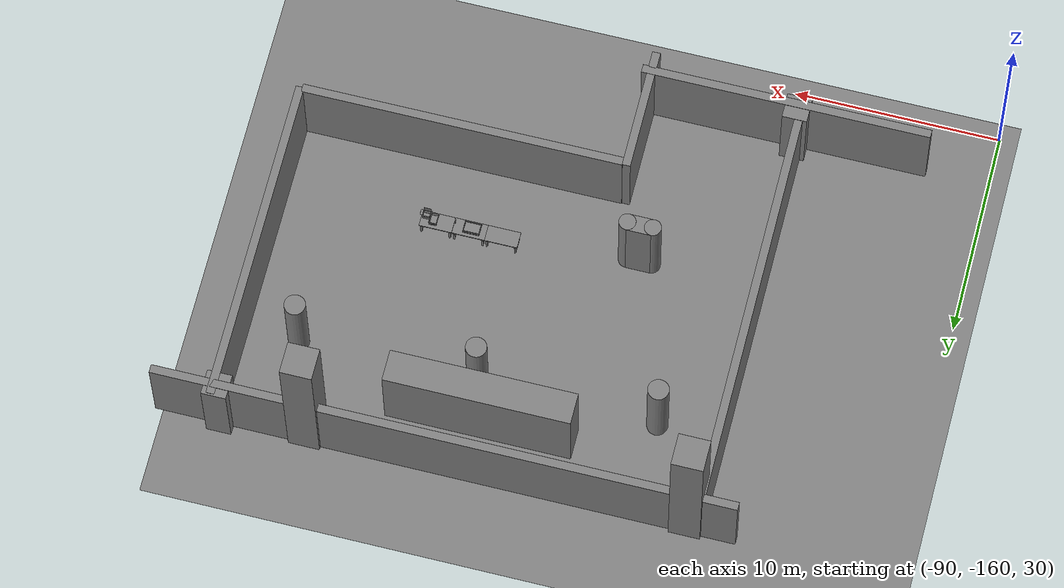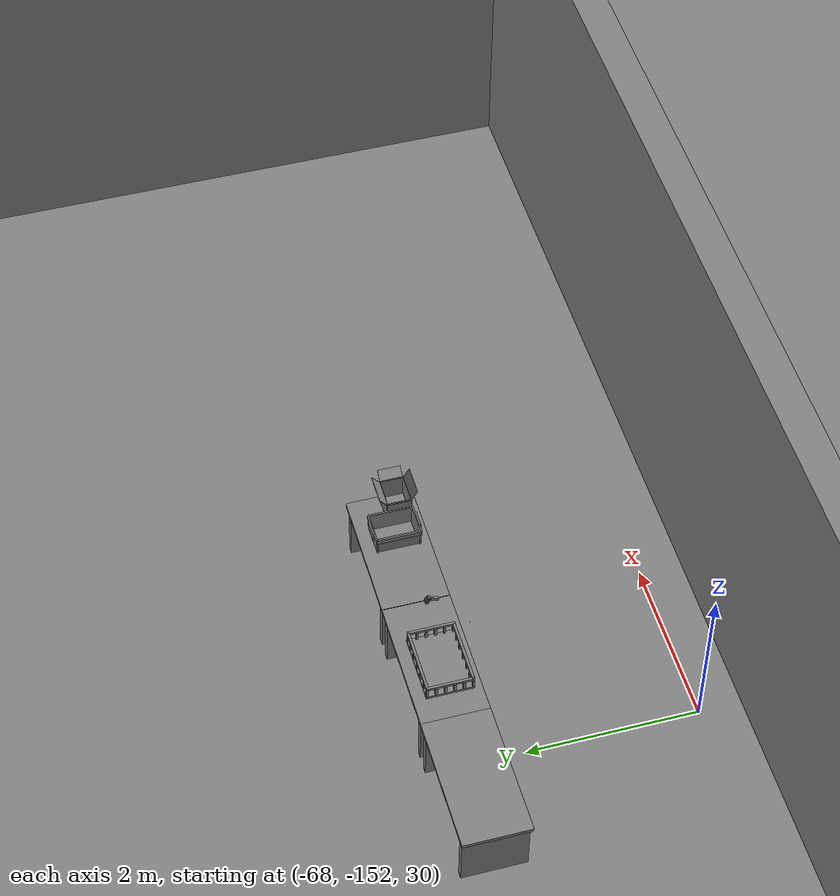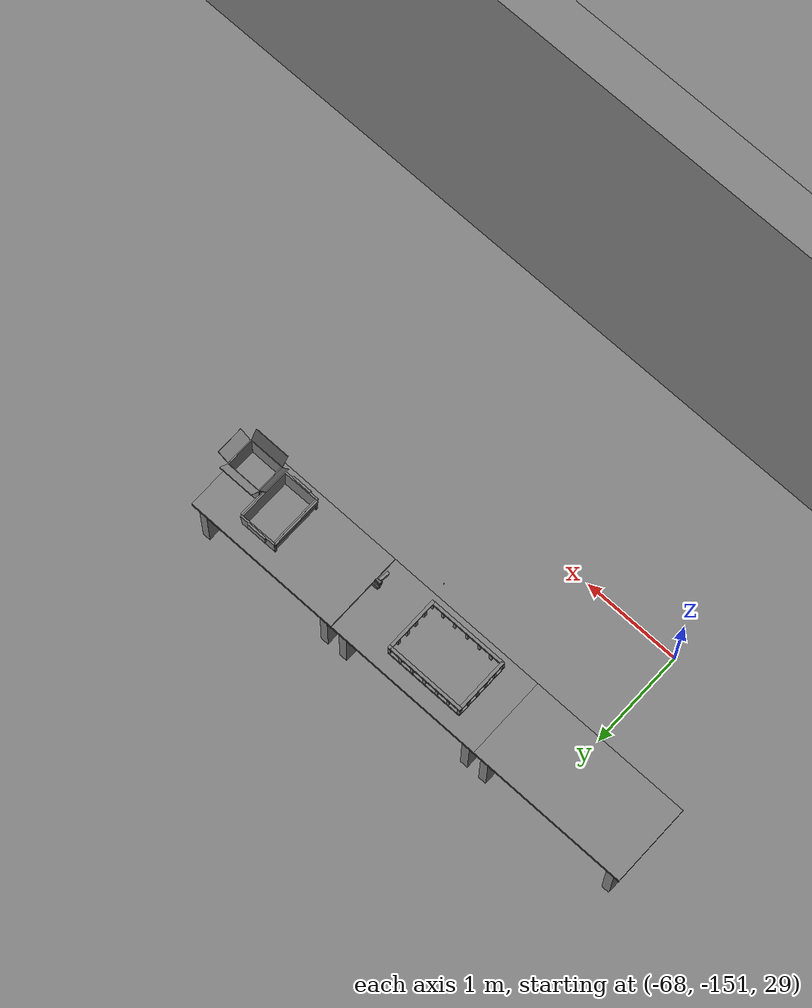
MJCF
<mujoco>
    <option gravity="0.000000000 0.000000000 -9.810000420" timestep="0.0049999999" integrator="implicitfast" density="1.225" viscosity="1.8000001e-05" noslip_iterations="10" iterations="100" sdf_iterations="50">
        <flag multiccd="disable"/>
    </option>
    <size memory="1000M"/>
    <compiler coordinate="local"/>
    <worldbody>
        <light cutoff="30" pos="0 1 1" dir="0 -1 -2"/>
        <light cutoff="30" pos="0 -1 1" dir="0 1 -2"/>
        <body pos="-64.866622925 -149.383972168 30.183746338" euler="89.999992371 89.999946594 0.000000000" name="openloong_gripper_2f85_fix_base_usda_bluebox_01">
            <geom contype="1" conaffinity="1" density="1000" type="box" material="" rgba="0.500000000 0.500000000 0.500000000 1.000000000" solimp="0.899999976 0.949999988 0.001000000" friction="1.000000000 0.005000000 0.000100000" solref="0.020000000 1.000000000" margin="0" condim="3" group="0" pos="0.276596069 0.187225342 0.000061035" quat="0.707107008 0.000077501 0.707106471 0.000077456" size="0.100000001 0.057999998 0.010000000" name="openloong_gripper_2f85_fix_base_usda_geom_3236FC50_4891_4891_A6AC_2F43EFF63F89"/>
            <geom contype="1" conaffinity="1" density="1000" type="box" material="" rgba="0.500000000 0.500000000 0.500000000 1.000000000" solimp="0.899999976 0.949999988 0.001000000" friction="1.000000000 0.005000000 0.000100000" solref="0.020000000 1.000000000" margin="0" condim="3" group="0" pos="0.000000000 0.002883911 0.000000000" quat="1.000000000 0.000000000 0.000000000 0.000000000" size="0.254000008 0.003000000 0.172000006" name="openloong_gripper_2f85_fix_base_usda_geom_5B04DAB0_D207_4462_A03E_231C994DABC3"/>
            <geom contype="1" conaffinity="1" density="1000" type="box" material="" rgba="0.500000000 0.500000000 0.500000000 1.000000000" solimp="0.899999976 0.949999988 0.001000000" friction="1.000000000 0.005000000 0.000100000" solref="0.020000000 1.000000000" margin="0" condim="3" group="0" pos="0.000015259 0.124874115 0.173477173" quat="0.999796450 0.020176515 -0.000000015 0.000000030" size="0.259999990 0.119999997 0.007000000" name="openloong_gripper_2f85_fix_base_usda_geom_29F3D729_9653_4928_8FCA_23B2E27F4E0F"/>
            <geom contype="1" conaffinity="1" density="1000" type="box" material="" rgba="0.500000000 0.500000000 0.500000000 1.000000000" solimp="0.899999976 0.949999988 0.001000000" friction="1.000000000 0.005000000 0.000100000" solref="0.020000000 1.000000000" margin="0" condim="3" group="0" pos="0.000015259 0.124874115 -0.173477173" quat="0.999796450 -0.020176545 -0.000000015 0.000000000" size="0.259999990 0.119999997 0.007000000" name="openloong_gripper_2f85_fix_base_usda_geom_9D5E63E7_0BE7_4EC7_AE5B_F069F0E1FC62"/>
            <geom contype="1" conaffinity="1" density="1000" type="box" material="" rgba="0.500000000 0.500000000 0.500000000 1.000000000" solimp="0.899999976 0.949999988 0.001000000" friction="1.000000000 0.005000000 0.000100000" solref="0.020000000 1.000000000" margin="0" condim="3" group="0" pos="0.000015259 0.214012146 0.188980103" quat="0.999913096 0.013176724 0.000000015 0.000000000" size="0.259999990 0.029999999 0.012500000" name="openloong_gripper_2f85_fix_base_usda_geom_0AD3A238_A8D7_40A2_95B4_B3E85D38C5ED"/>
            <geom contype="1" conaffinity="1" density="1000" type="box" material="" rgba="0.500000000 0.500000000 0.500000000 1.000000000" solimp="0.899999976 0.949999988 0.001000000" friction="1.000000000 0.005000000 0.000100000" solref="0.020000000 1.000000000" margin="0" condim="3" group="0" pos="-0.258346558 0.125289917 0.001876831" quat="0.702796996 -0.020792052 0.710783184 0.020769238" size="0.189999998 0.119999997 0.009000000" name="openloong_gripper_2f85_fix_base_usda_geom_49CEA940_EBDC_4CDF_8BE4_60A3A6AE4814"/>
            <geom contype="1" conaffinity="1" density="1000" type="box" material="" rgba="0.500000000 0.500000000 0.500000000 1.000000000" solimp="0.899999976 0.949999988 0.001000000" friction="1.000000000 0.005000000 0.000100000" solref="0.020000000 1.000000000" margin="0" condim="3" group="0" pos="0.000015259 0.214012146 -0.188980103" quat="0.999913096 -0.013176769 0.000000030 0.000000015" size="0.259999990 0.029999999 0.012500000" name="openloong_gripper_2f85_fix_base_usda_geom_EDE6E09F_7814_431D_A341_0496012EB03B"/>
            <geom contype="1" conaffinity="1" density="1000" type="box" material="" rgba="0.500000000 0.500000000 0.500000000 1.000000000" solimp="0.899999976 0.949999988 0.001000000" friction="1.000000000 0.005000000 0.000100000" solref="0.020000000 1.000000000" margin="0" condim="3" group="0" pos="-0.276596069 0.187225342 0.000061035" quat="0.707106650 0.000077441 0.707106709 0.000077456" size="0.100000001 0.057999998 0.010000000" name="openloong_gripper_2f85_fix_base_usda_geom_5137EB0E_448B_4211_A6AD_100B50E04DD0"/>
            <geom contype="1" conaffinity="1" density="1000" type="box" material="" rgba="0.500000000 0.500000000 0.500000000 1.000000000" solimp="0.899999976 0.949999988 0.001000000" friction="1.000000000 0.005000000 0.000100000" solref="0.020000000 1.000000000" margin="0" condim="3" group="0" pos="0.258346558 0.125289917 0.001876831" quat="0.702851534 0.018856451 0.710823834 -0.019329429" size="0.189999998 0.119999997 0.009000000" name="openloong_gripper_2f85_fix_base_usda_geom_3B940B1F_1160_4AD8_8F6F_F9DD25662902"/>
            <freejoint name="openloong_gripper_2f85_fix_base_usda_bluebox_01_joint"/>
            <site size="0.005000000 0.005000000 0.005000000" rgba="0.500000000 0.500000000 0.500000000 1.000000000" pos="0.000000000 0.000000000 0.000000000" quat="0.999961913 0.008726534 0.000000000 0.000000000" group="0" type="sphere" name="openloong_gripper_2f85_fix_base_usda_bluebox_01site"/>
        </body>
        <body pos="-64.496299744 -149.491867065 30.235729218" euler="0.000000000 0.000000000 89.999946594" name="openloong_gripper_2f85_fix_base_usda_cardboardbox_01">
            <geom contype="1" conaffinity="1" density="1000" type="box" material="" rgba="0.500000000 0.500000000 0.500000000 1.000000000" solimp="0.899999976 0.949999988 0.001000000" friction="1.000000000 0.005000000 0.000100000" solref="0.020000000 1.000000000" margin="0" condim="3" group="0" pos="-0.003166199 -0.004086494 0.005052090" quat="1.000000000 0.000000000 0.000000000 0.000000000" size="0.142499998 0.177500010 0.005000000" name="openloong_gripper_2f85_fix_base_usda_geom_8D2A77CE_3462_44B8_83E6_EEEAC8899372"/>
            <geom contype="1" conaffinity="1" density="1000" type="box" material="" rgba="0.500000000 0.500000000 0.500000000 1.000000000" solimp="0.899999976 0.949999988 0.001000000" friction="1.000000000 0.005000000 0.000100000" solref="0.020000000 1.000000000" margin="0" condim="3" group="0" pos="-0.003166199 0.170316696 0.150570869" quat="1.000000000 0.000000000 0.000000000 0.000000000" size="0.142499998 0.005000000 0.149999991" name="openloong_gripper_2f85_fix_base_usda_geom_2AF23257_442A_4633_AB53_F6E7EE24A197"/>
            <geom contype="1" conaffinity="1" density="1000" type="box" material="" rgba="0.500000000 0.500000000 0.500000000 1.000000000" solimp="0.899999976 0.949999988 0.001000000" friction="1.000000000 0.005000000 0.000100000" solref="0.020000000 1.000000000" margin="0" condim="3" group="0" pos="-0.147399902 -0.005307198 0.150570869" quat="1.000000000 0.000000000 0.000000000 0.000000000" size="0.005000000 0.177500010 0.149999991" name="openloong_gripper_2f85_fix_base_usda_geom_FF8E1D67_AEEC_4F9D_91AB_E5DA06CFA439"/>
            <geom contype="1" conaffinity="1" density="1000" type="box" material="" rgba="0.500000000 0.500000000 0.500000000 1.000000000" solimp="0.899999976 0.949999988 0.001000000" friction="1.000000000 0.005000000 0.000100000" solref="0.020000000 1.000000000" margin="0" condim="3" group="0" pos="0.140275955 -0.005307198 0.150570869" quat="1.000000000 0.000000000 0.000000000 0.000000000" size="0.005000000 0.177500010 0.149999991" name="openloong_gripper_2f85_fix_base_usda_geom_C720B286_E76D_4693_ADD4_D3277AD7D97C"/>
            <geom contype="1" conaffinity="1" density="1000" type="box" material="" rgba="0.500000000 0.500000000 0.500000000 1.000000000" solimp="0.899999976 0.949999988 0.001000000" friction="1.000000000 0.005000000 0.000100000" solref="0.020000000 1.000000000" margin="0" condim="3" group="0" pos="-0.003166199 -0.181550980 0.150570869" quat="1.000000000 0.000000000 0.000000000 0.000000000" size="0.142499998 0.005000000 0.149999991" name="openloong_gripper_2f85_fix_base_usda_geom_E7B04C59_6F4F_4266_981A_AB290D48F70D"/>
            <freejoint name="openloong_gripper_2f85_fix_base_usda_cardboardbox_01_joint"/>
            <site size="0.005000000 0.005000000 0.005000000" rgba="0.500000000 0.500000000 0.500000000 1.000000000" pos="0.000000000 0.000000000 0.000000000" quat="0.999961913 0.008726535 0.000000000 0.000000000" group="0" type="sphere" name="openloong_gripper_2f85_fix_base_usda_site_46CD0B27_F620_4F48_B130_BD9FE9849DA9"/>
            <body pos="0.139160156 -0.004048347 0.301930904" euler="-179.999954224 49.383502960 179.999954224" name="openloong_gripper_2f85_fix_base_usda_A1_006">
                <geom contype="1" conaffinity="1" density="1000" type="box" material="" rgba="0.500000000 0.500000000 0.500000000 1.000000000" solimp="0.899999976 0.949999988 0.001000000" friction="1.000000000 0.005000000 0.000100000" solref="0.020000000 1.000000000" margin="0" condim="3" group="0" pos="-0.071587563 0.000009537 0.001745224" quat="0.999999881 0.000000000 0.000000000 0.000000000" size="0.071249999 0.179999992 0.002500000" name="openloong_gripper_2f85_fix_base_usda_geom_01E00F9D_A698_45E7_AF9B_F1092D775961"/>
                <joint armature="0" stiffness="0.07" damping="0.0099999998" axis="0.000000 1.000000 0.000000" type="hinge" name="openloong_gripper_2f85_fix_base_usda_A1_006"/>
            </body>
            <body pos="-0.145902634 -0.004086494 0.301938057" euler="-180.000000000 -60.000011444 -180.000000000" name="openloong_gripper_2f85_fix_base_usda_A2_006">
                <geom contype="1" conaffinity="1" density="1000" type="box" material="" rgba="0.500000000 0.500000000 0.500000000 1.000000000" solimp="0.899999976 0.949999988 0.001000000" friction="1.000000000 0.005000000 0.000100000" solref="0.020000000 1.000000000" margin="0" condim="3" group="0" pos="0.071268082 0.000009537 0.002717972" quat="0.000002921 0.000000000 -0.000000030 0.999999881" size="0.071249999 0.179999992 0.002500000" name="openloong_gripper_2f85_fix_base_usda_geom_F64D6633_ECEC_4731_B494_9DEB613026F8"/>
                <joint armature="0" stiffness="0.07" damping="0.0099999998" axis="0.000000 1.000000 0.000000" type="hinge" name="openloong_gripper_2f85_fix_base_usda_A2_006"/>
            </body>
            <body pos="-0.003385544 0.175991058 0.301930904" euler="-125.858116150 -0.000004561 0.000002331" name="openloong_gripper_2f85_fix_base_usda_B2_006">
                <geom contype="1" conaffinity="1" density="1000" type="box" material="" rgba="0.500000000 0.500000000 0.500000000 1.000000000" solimp="0.899999976 0.949999988 0.001000000" friction="1.000000000 0.005000000 0.000100000" solref="0.020000000 1.000000000" margin="0" condim="3" group="0" pos="0.000009537 -0.070939064 -0.002470016" quat="0.999614120 0.027776197 -0.000000015 0.000000030" size="0.137500003 0.064999998 0.005000000" name="openloong_gripper_2f85_fix_base_usda_geom_2C2A179B_EF3C_41E7_99ED_8442B6A198A8"/>
                <joint armature="0" stiffness="0.07" damping="0.0099999998" axis="1.000000 0.000000 0.000000" type="hinge" name="openloong_gripper_2f85_fix_base_usda_B2_006"/>
            </body>
            <body pos="-0.003385544 -0.184140205 0.301938057" euler="147.805557251 0.000000000 0.000000000" name="openloong_gripper_2f85_fix_base_usda_B1_006">
                <geom contype="1" conaffinity="1" density="1000" type="box" material="" rgba="0.500000000 0.500000000 0.500000000 1.000000000" solimp="0.899999976 0.949999988 0.001000000" friction="1.000000000 0.005000000 0.000100000" solref="0.020000000 1.000000000" margin="0" condim="3" group="0" pos="-0.000028610 0.070202351 -0.002703667" quat="0.999614179 -0.027776167 0.000000000 0.000000000" size="0.137500003 0.064999998 0.005000000" name="openloong_gripper_2f85_fix_base_usda_geom_7B8F57F7_2065_4517_A5CD_3EA25AEBE849"/>
                <joint armature="0" stiffness="0.07" damping="0.0099999998" axis="1.000000 0.000000 0.000000" type="hinge" name="openloong_gripper_2f85_fix_base_usda_B1_006"/>
            </body>
        </body>
        <body pos="-65.882858276 -149.481979370 30.229999542" euler="-64.487716675 0.000000000 0.000000000" name="openloong_gripper_2f85_fix_base_usda_Barcode">
            <geom contype="1" conaffinity="1" density="1000" type="box" material="" rgba="0.500000000 0.500000000 0.500000000 1.000000000" solimp="0.899999976 0.949999988 0.001000000" friction="1.000000000 0.005000000 0.000100000" solref="0.020000000 1.000000000" margin="0" condim="3" group="0" pos="0.000000000 0.013038635 0.001419067" quat="0.000000000 0.000000000 0.000000000 1.000000119" size="0.034000002 0.010000000 0.017999999" name="openloong_gripper_2f85_fix_base_usda_geom_9FE0A9FA_F337_481B_90F2_8F0DBF5FC4F7"/>
            <geom contype="1" conaffinity="1" density="1000" type="box" material="" rgba="0.500000000 0.500000000 0.500000000 1.000000000" solimp="0.899999976 0.949999988 0.001000000" friction="1.000000000 0.005000000 0.000100000" solref="0.020000000 1.000000000" margin="0" condim="3" group="0" pos="0.000000000 -0.035301208 -0.007095337" quat="0.000000000 0.000000000 -0.043619365 0.999048233" size="0.028999999 0.010000000 0.020000000" name="openloong_gripper_2f85_fix_base_usda_geom_F65B1AAD_111A_4D7B_9BD8_8B1556F5054B"/>
            <geom contype="1" conaffinity="1" density="1000" type="box" material="" rgba="0.500000000 0.500000000 0.500000000 1.000000000" solimp="0.899999976 0.949999988 0.001000000" friction="1.000000000 0.005000000 0.000100000" solref="0.020000000 1.000000000" margin="0" condim="3" group="0" pos="0.000000000 -0.043411255 -0.011749268" quat="0.922262907 0.386563420 0.000000000 0.000000000" size="0.026000001 0.010000000 0.020000000" name="openloong_gripper_2f85_fix_base_usda_geom_F1F39C95_F6C8_417F_B8E3_5177A5CC43FE"/>
            <geom contype="1" conaffinity="1" density="1000" type="box" material="" rgba="0.500000000 0.500000000 0.500000000 1.000000000" solimp="0.899999976 0.949999988 0.001000000" friction="1.000000000 0.005000000 0.000100000" solref="0.020000000 1.000000000" margin="0" condim="3" group="0" pos="0.000000000 -0.016967773 -0.031860352" quat="0.000000000 0.000000000 0.000000000 1.000000119" size="0.008000000 0.010000000 0.013000000" name="openloong_gripper_2f85_fix_base_usda_geom_BEF2E729_5690_4262_97AE_099BD8FCF1AB"/>
            <geom contype="1" conaffinity="1" density="1000" type="box" material="" rgba="0.500000000 0.500000000 0.500000000 1.000000000" solimp="0.899999976 0.949999988 0.001000000" friction="1.000000000 0.005000000 0.000100000" solref="0.020000000 1.000000000" margin="0" condim="3" group="0" pos="0.000000000 -0.001869202 0.000312805" quat="0.953716993 0.300705761 0.000000000 0.000000000" size="0.032000002 0.010000000 0.018999999" name="openloong_gripper_2f85_fix_base_usda_geom_65B02343_083E_4AD9_96BF_8067C9BD3A22"/>
            <geom contype="1" conaffinity="1" density="1000" type="box" material="" rgba="0.500000000 0.500000000 0.500000000 1.000000000" solimp="0.899999976 0.949999988 0.001000000" friction="1.000000000 0.005000000 0.000100000" solref="0.020000000 1.000000000" margin="0" condim="3" group="0" pos="0.000000000 -0.019531250 -0.003173828" quat="0.953716993 0.300705761 0.000000000 0.000000000" size="0.030999999 0.010000000 0.020000000" name="openloong_gripper_2f85_fix_base_usda_geom_3BDCD353_1280_4EB6_B713_EDEEEC14C99D"/>
            <geom contype="1" conaffinity="1" density="1000" type="box" material="" rgba="0.500000000 0.500000000 0.500000000 1.000000000" solimp="0.899999976 0.949999988 0.001000000" friction="1.000000000 0.005000000 0.000100000" solref="0.020000000 1.000000000" margin="0" condim="3" group="0" pos="0.000000000 -0.035301208 -0.007095337" quat="0.953716993 0.300705761 0.000000000 0.000000000" size="0.028999999 0.010000000 0.020000000" name="openloong_gripper_2f85_fix_base_usda_geom_AF4F2156_8A3C_464B_A633_45625D3F08AD"/>
            <geom contype="1" conaffinity="1" density="1000" type="box" material="" rgba="0.500000000 0.500000000 0.500000000 1.000000000" solimp="0.899999976 0.949999988 0.001000000" friction="1.000000000 0.005000000 0.000100000" solref="0.020000000 1.000000000" margin="0" condim="3" group="0" pos="0.000000000 -0.042617798 -0.071121216" quat="0.000000000 0.000000000 0.000000000 1.000000119" size="0.013000000 0.021000000 0.059999999" name="openloong_gripper_2f85_fix_base_usda_geom_E055D657_5FB5_4736_9046_A63D993D8E74"/>
            <freejoint name="openloong_gripper_2f85_fix_base_usda_Barcode_joint"/>
            <site size="0.005000000 0.005000000 0.005000000" rgba="0.500000000 0.500000000 0.500000000 1.000000000" pos="0.000000000 0.000000000 0.000000000" quat="1.000000000 0.000000000 0.000000000 0.000000000" group="0" type="sphere" name="openloong_gripper_2f85_fix_base_usda_Barcode_site"/>
        </body>
        <body pos="-66.745018005 -149.392349243 30.184000015" euler="0.000000000 0.000000000 89.999946594" name="[22333109208063]_Basket_01">
            <geom contype="1" conaffinity="1" density="1000" type="box" material="" rgba="0.500000000 0.500000000 0.500000000 1.000000000" solimp="0.899999976 0.949999988 0.001000000" friction="1.000000000 0.005000000 0.000100000" solref="0.020000000 1.000000000" margin="0" condim="3" group="0" pos="-0.052425385 0.389207840 0.089787483" quat="0.707107008 0.000000000 0.000000000 0.707106411" size="0.014249999 0.014249999 0.059999999" name="[22333109208063]_geom_8C5A9420_B26E_4AAF_B10E_D23993821923"/>
            <geom contype="1" conaffinity="1" density="1000" type="box" material="" rgba="0.500000000 0.500000000 0.500000000 1.000000000" solimp="0.899999976 0.949999988 0.001000000" friction="1.000000000 0.005000000 0.000100000" solref="0.020000000 1.000000000" margin="0" condim="3" group="0" pos="0.264015198 -0.133043289 0.089787483" quat="0.707107008 0.000000000 0.000000000 0.707106411" size="0.014249999 0.014249999 0.059999999" name="[22333109208063]_geom_B3A61DF3_2468_4980_ABBF_9CD29BA127CD"/>
            <geom contype="1" conaffinity="1" density="1000" type="box" material="" rgba="0.500000000 0.500000000 0.500000000 1.000000000" solimp="0.899999976 0.949999988 0.001000000" friction="1.000000000 0.005000000 0.000100000" solref="0.020000000 1.000000000" margin="0" condim="3" group="0" pos="-0.264015198 -0.265548706 0.089793205" quat="0.707107008 0.000000000 0.000000000 0.707106411" size="0.014249999 0.014249999 0.059999999" name="[22333109208063]_geom_9FA8573E_AB54_46FA_886D_9E747A0BF19A"/>
            <geom contype="1" conaffinity="1" density="1000" type="box" material="" rgba="0.500000000 0.500000000 0.500000000 1.000000000" solimp="0.899999976 0.949999988 0.001000000" friction="1.000000000 0.005000000 0.000100000" solref="0.020000000 1.000000000" margin="0" condim="3" group="0" pos="-0.160263062 -0.389322281 0.089793205" quat="0.707107008 0.000000000 0.000000000 0.707106411" size="0.014249999 0.014249999 0.059999999" name="[22333109208063]_geom_F2DE82CB_3F6E_43B7_8C0C_57DF22417BBD"/>
            <geom contype="1" conaffinity="1" density="1000" type="box" material="" rgba="0.500000000 0.500000000 0.500000000 1.000000000" solimp="0.899999976 0.949999988 0.001000000" friction="1.000000000 0.005000000 0.000100000" solref="0.020000000 1.000000000" margin="0" condim="3" group="0" pos="0.162265778 -0.389322281 0.089787483" quat="0.707107008 0.000000000 0.000000000 0.707106411" size="0.014249999 0.014249999 0.059999999" name="[22333109208063]_geom_E9405680_BEE4_4323_BE14_2EDD41865A23"/>
            <geom contype="1" conaffinity="1" density="1000" type="box" material="" rgba="0.500000000 0.500000000 0.500000000 1.000000000" solimp="0.899999976 0.949999988 0.001000000" friction="1.000000000 0.005000000 0.000100000" solref="0.020000000 1.000000000" margin="0" condim="3" group="0" pos="0.264015198 0.389207840 0.089787483" quat="0.707107008 0.000000000 0.000000000 0.707106411" size="0.014249999 0.014249999 0.059999999" name="[22333109208063]_geom_EFFE5326_54D9_4097_B845_75711A0199D0"/>
            <geom contype="1" conaffinity="1" density="1000" type="box" material="" rgba="0.500000000 0.500000000 0.500000000 1.000000000" solimp="0.899999976 0.949999988 0.001000000" friction="1.000000000 0.005000000 0.000100000" solref="0.020000000 1.000000000" margin="0" condim="3" group="0" pos="-0.264015198 -0.133043289 0.089793205" quat="0.707107008 0.000000000 0.000000000 0.707106411" size="0.014249999 0.014249999 0.059999999" name="[22333109208063]_geom_68B68AF5_A1F2_48F4_9DB3_C90971901771"/>
            <geom contype="1" conaffinity="1" density="1000" type="box" material="" rgba="0.500000000 0.500000000 0.500000000 1.000000000" solimp="0.899999976 0.949999988 0.001000000" friction="1.000000000 0.005000000 0.000100000" solref="0.020000000 1.000000000" margin="0" condim="3" group="0" pos="-0.264026642 0.269256592 0.089793205" quat="0.707107008 0.000000000 0.000000000 0.707106411" size="0.014249999 0.014249999 0.059999999" name="[22333109208063]_geom_8F111419_56AF_4622_A673_8113AB16FAE5"/>
            <geom contype="1" conaffinity="1" density="1000" type="box" material="" rgba="0.500000000 0.500000000 0.500000000 1.000000000" solimp="0.899999976 0.949999988 0.001000000" friction="1.000000000 0.005000000 0.000100000" solref="0.020000000 1.000000000" margin="0" condim="3" group="0" pos="0.054462433 0.389207840 0.089787483" quat="0.707107008 0.000000000 0.000000000 0.707106411" size="0.014249999 0.014249999 0.059999999" name="[22333109208063]_geom_7D8EBF99_7337_4150_A347_7556D5C5AFEB"/>
            <geom contype="1" conaffinity="1" density="1000" type="box" material="" rgba="0.500000000 0.500000000 0.500000000 1.000000000" solimp="0.899999976 0.949999988 0.001000000" friction="1.000000000 0.005000000 0.000100000" solref="0.020000000 1.000000000" margin="0" condim="3" group="0" pos="0.054462433 -0.389322281 0.089787483" quat="0.707107008 0.000000000 0.000000000 0.707106411" size="0.014249999 0.014249999 0.059999999" name="[22333109208063]_geom_5A3DC8A3_BAAD_4232_99FF_9B7AD33A93B3"/>
            <geom contype="1" conaffinity="1" density="1000" type="box" material="" rgba="0.500000000 0.500000000 0.500000000 1.000000000" solimp="0.899999976 0.949999988 0.001000000" friction="1.000000000 0.005000000 0.000100000" solref="0.020000000 1.000000000" margin="0" condim="3" group="0" pos="0.264015198 0.269256592 0.089793205" quat="0.707107008 0.000000000 0.000000000 0.707106411" size="0.014249999 0.014249999 0.059999999" name="[22333109208063]_geom_72A64347_C7CD_4A02_A932_91970453BCF3"/>
            <geom contype="1" conaffinity="1" density="1000" type="box" material="" rgba="0.500000000 0.500000000 0.500000000 1.000000000" solimp="0.899999976 0.949999988 0.001000000" friction="1.000000000 0.005000000 0.000100000" solref="0.020000000 1.000000000" margin="0" condim="3" group="0" pos="0.264015198 -0.389322281 0.089787483" quat="0.707107008 0.000000000 0.000000000 0.707106411" size="0.014249999 0.014249999 0.059999999" name="[22333109208063]_geom_466E9F0C_18CB_4991_B3C1_EF1DDE5AEBD9"/>
            <geom contype="1" conaffinity="1" density="1000" type="box" material="" rgba="0.500000000 0.500000000 0.500000000 1.000000000" solimp="0.899999976 0.949999988 0.001000000" friction="1.000000000 0.005000000 0.000100000" solref="0.020000000 1.000000000" margin="0" condim="3" group="0" pos="0.000000000 0.000000000 0.015998840" quat="0.707107008 0.000000000 0.000000000 0.707106411" size="0.403499991 0.279000014 0.015750000" name="[22333109208063]_geom_EE95CE99_0B47_4827_B948_8D80BA6E2ADC"/>
            <geom contype="1" conaffinity="1" density="1000" type="box" material="" rgba="0.500000000 0.500000000 0.500000000 1.000000000" solimp="0.899999976 0.949999988 0.001000000" friction="1.000000000 0.005000000 0.000100000" solref="0.020000000 1.000000000" margin="0" condim="3" group="0" pos="0.000000000 -0.389476776 0.163619041" quat="0.707107008 0.000000000 0.000000000 0.707106411" size="0.015000000 0.277500004 0.015750000" name="[22333109208063]_geom_5290505B_6A8E_4011_A1A4_D0E85938B763"/>
            <geom contype="1" conaffinity="1" density="1000" type="box" material="" rgba="0.500000000 0.500000000 0.500000000 1.000000000" solimp="0.899999976 0.949999988 0.001000000" friction="1.000000000 0.005000000 0.000100000" solref="0.020000000 1.000000000" margin="0" condim="3" group="0" pos="0.162265778 0.389207840 0.089787483" quat="0.707107008 0.000000000 0.000000000 0.707106411" size="0.014249999 0.014249999 0.059999999" name="[22333109208063]_geom_10902674_5FAD_4555_BAA1_6EE1BEA8556C"/>
            <geom contype="1" conaffinity="1" density="1000" type="box" material="" rgba="0.500000000 0.500000000 0.500000000 1.000000000" solimp="0.899999976 0.949999988 0.001000000" friction="1.000000000 0.005000000 0.000100000" solref="0.020000000 1.000000000" margin="0" condim="3" group="0" pos="0.000000000 0.389471054 0.163619041" quat="0.707107008 0.000000000 0.000000000 0.707106411" size="0.015000000 0.277500004 0.015750000" name="[22333109208063]_geom_38C38F6B_2AD9_4FCF_A65A_623C288BAF44"/>
            <geom contype="1" conaffinity="1" density="1000" type="box" material="" rgba="0.500000000 0.500000000 0.500000000 1.000000000" solimp="0.899999976 0.949999988 0.001000000" friction="1.000000000 0.005000000 0.000100000" solref="0.020000000 1.000000000" margin="0" condim="3" group="0" pos="-0.263511658 0.000000000 0.163619041" quat="0.707107008 0.000000000 0.000000000 0.707106411" size="0.403499991 0.015000000 0.015750000" name="[22333109208063]_geom_1DF01885_98FA_462E_B73A_F2A7150FBF79"/>
            <geom contype="1" conaffinity="1" density="1000" type="box" material="" rgba="0.500000000 0.500000000 0.500000000 1.000000000" solimp="0.899999976 0.949999988 0.001000000" friction="1.000000000 0.005000000 0.000100000" solref="0.020000000 1.000000000" margin="0" condim="3" group="0" pos="-0.264015198 0.141334534 0.089793205" quat="0.707107008 0.000000000 0.000000000 0.707106411" size="0.014249999 0.014249999 0.059999999" name="[22333109208063]_geom_AA72409B_6077_4CEC_B4F5_EA1BF44696D8"/>
            <geom contype="1" conaffinity="1" density="1000" type="box" material="" rgba="0.500000000 0.500000000 0.500000000 1.000000000" solimp="0.899999976 0.949999988 0.001000000" friction="1.000000000 0.005000000 0.000100000" solref="0.020000000 1.000000000" margin="0" condim="3" group="0" pos="0.264015198 -0.265548706 0.089787483" quat="0.707107008 0.000000000 0.000000000 0.707106411" size="0.014249999 0.014249999 0.059999999" name="[22333109208063]_geom_66B2E3D5_6E07_4E2A_9D32_12A764805E12"/>
            <geom contype="1" conaffinity="1" density="1000" type="box" material="" rgba="0.500000000 0.500000000 0.500000000 1.000000000" solimp="0.899999976 0.949999988 0.001000000" friction="1.000000000 0.005000000 0.000100000" solref="0.020000000 1.000000000" margin="0" condim="3" group="0" pos="-0.160263062 0.389207840 0.089787483" quat="0.707107008 0.000000000 0.000000000 0.707106411" size="0.014249999 0.014249999 0.059999999" name="[22333109208063]_geom_1019344F_A5D7_459A_BF47_0D73DC4BCBD1"/>
            <geom contype="1" conaffinity="1" density="1000" type="box" material="" rgba="0.500000000 0.500000000 0.500000000 1.000000000" solimp="0.899999976 0.949999988 0.001000000" friction="1.000000000 0.005000000 0.000100000" solref="0.020000000 1.000000000" margin="0" condim="3" group="0" pos="-0.052425385 -0.389322281 0.089787483" quat="0.707107008 0.000000000 0.000000000 0.707106411" size="0.014249999 0.014249999 0.059999999" name="[22333109208063]_geom_DC5D507A_9B57_4EB2_9291_87A01F6E0C91"/>
            <geom contype="1" conaffinity="1" density="1000" type="box" material="" rgba="0.500000000 0.500000000 0.500000000 1.000000000" solimp="0.899999976 0.949999988 0.001000000" friction="1.000000000 0.005000000 0.000100000" solref="0.020000000 1.000000000" margin="0" condim="3" group="0" pos="-0.264026642 -0.389322281 0.089793205" quat="0.707107008 0.000000000 0.000000000 0.707106411" size="0.014249999 0.014249999 0.059999999" name="[22333109208063]_geom_B06EB2FA_6C09_43F9_A0F6_1F3D25F79F02"/>
            <geom contype="1" conaffinity="1" density="1000" type="box" material="" rgba="0.500000000 0.500000000 0.500000000 1.000000000" solimp="0.899999976 0.949999988 0.001000000" friction="1.000000000 0.005000000 0.000100000" solref="0.020000000 1.000000000" margin="0" condim="3" group="0" pos="0.264015198 0.141334534 0.089787483" quat="0.707107008 0.000000000 0.000000000 0.707106411" size="0.014249999 0.014249999 0.059999999" name="[22333109208063]_geom_8A9A18B1_C4D6_40F4_AD66_CFF329316604"/>
            <geom contype="1" conaffinity="1" density="1000" type="box" material="" rgba="0.500000000 0.500000000 0.500000000 1.000000000" solimp="0.899999976 0.949999988 0.001000000" friction="1.000000000 0.005000000 0.000100000" solref="0.020000000 1.000000000" margin="0" condim="3" group="0" pos="-0.264015198 0.389207840 0.089793205" quat="0.707107008 0.000000000 0.000000000 0.707106411" size="0.014249999 0.014249999 0.059999999" name="[22333109208063]_geom_02A8CEF2_54D7_4CC3_9C78_5C325F5E9F55"/>
            <geom contype="1" conaffinity="1" density="1000" type="box" material="" rgba="0.500000000 0.500000000 0.500000000 1.000000000" solimp="0.899999976 0.949999988 0.001000000" friction="1.000000000 0.005000000 0.000100000" solref="0.020000000 1.000000000" margin="0" condim="3" group="0" pos="0.264015198 0.004480362 0.089787483" quat="0.707107008 0.000000000 0.000000000 0.707106411" size="0.014249999 0.014249999 0.059999999" name="[22333109208063]_geom_34462EA8_EC53_479A_8C60_50DF136E8667"/>
            <geom contype="1" conaffinity="1" density="1000" type="box" material="" rgba="0.500000000 0.500000000 0.500000000 1.000000000" solimp="0.899999976 0.949999988 0.001000000" friction="1.000000000 0.005000000 0.000100000" solref="0.020000000 1.000000000" margin="0" condim="3" group="0" pos="0.263694763 -0.000011444 0.163619041" quat="0.707107008 0.000000000 0.000000000 0.707106411" size="0.403499991 0.015000000 0.015750000" name="[22333109208063]_geom_85007C6A_F5FA_4775_B8AF_C1C9FADC382E"/>
            <geom contype="1" conaffinity="1" density="1000" type="box" material="" rgba="0.500000000 0.500000000 0.500000000 1.000000000" solimp="0.899999976 0.949999988 0.001000000" friction="1.000000000 0.005000000 0.000100000" solref="0.020000000 1.000000000" margin="0" condim="3" group="0" pos="-0.264015198 0.004480362 0.089793205" quat="0.707107008 0.000000000 0.000000000 0.707106411" size="0.014249999 0.014249999 0.059999999" name="[22333109208063]_geom_5052EBD5_5A9C_4089_AF4F_0158CB050DB5"/>
            <freejoint name="[22333109208063]_joint_0F19FBDF_1103_42B8_88C2_D708AE939888"/>
        </body>
        <body pos="0.000000000 0.000000000 0.000000000" euler="0.000000000 0.000000000 0.000000000" name="Static Objects_Static Objects">
            <geom contype="1" conaffinity="1" density="1000" type="box" material="" rgba="0.500000000 0.500000000 0.500000000 1.000000000" solimp="0.899999976 0.949999988 0.001000000" friction="1.000000000 0.005000000 0.000100000" solref="0.020000000 1.000000000" margin="0" condim="3" group="0" pos="-67.544113159 -149.365814209 29.727830887" quat="0.500000417 0.499999970 0.499999553 0.499999970" size="0.381000012 0.319999993 0.041000001" name="Static Objects_geom_E164448D_AA25_4136_B7D0_0B1E382B7D26"/>
            <geom contype="1" conaffinity="1" density="1000" type="box" material="" rgba="0.500000000 0.500000000 0.500000000 1.000000000" solimp="0.899999976 0.949999988 0.001000000" friction="1.000000000 0.005000000 0.000100000" solref="0.020000000 1.000000000" margin="0" condim="3" group="0" pos="-68.239501953 -149.365814209 30.086868286" quat="0.500000417 0.499999970 0.499999553 0.499999970" size="0.370999992 0.039500002 0.745000005" name="Static Objects_geom_B740CE24_63F5_443E_8053_244155DD0031"/>
            <geom contype="1" conaffinity="1" density="1000" type="box" material="" rgba="0.500000000 0.500000000 0.500000000 1.000000000" solimp="0.899999976 0.949999988 0.001000000" friction="1.000000000 0.005000000 0.000100000" solref="0.020000000 1.000000000" margin="0" condim="3" group="0" pos="-68.239501953 -149.365814209 30.147235870" quat="0.500000417 0.499999970 0.499999553 0.499999970" size="0.400000006 0.022000000 0.800000012" name="Static Objects_geom_402D8729_95A3_4129_90E0_6BEACA864C64"/>
            <geom contype="1" conaffinity="1" density="1000" type="box" material="" rgba="0.500000000 0.500000000 0.500000000 1.000000000" solimp="0.899999976 0.949999988 0.001000000" friction="1.000000000 0.005000000 0.000100000" solref="0.020000000 1.000000000" margin="0" condim="3" group="0" pos="-68.934890747 -149.365814209 29.727830887" quat="0.500000417 0.499999970 0.499999553 0.499999970" size="0.381000012 0.319999993 0.041000001" name="Static Objects_geom_9F14C6FE_2440_49D4_9A53_618B349B633F"/>
            <geom contype="1" conaffinity="1" density="1000" type="box" material="" rgba="0.500000000 0.500000000 0.500000000 1.000000000" solimp="0.899999976 0.949999988 0.001000000" friction="1.000000000 0.005000000 0.000100000" solref="0.020000000 1.000000000" margin="0" condim="3" group="0" pos="-68.239501953 -149.365814209 29.561563492" quat="0.500000417 0.499999970 0.499999553 0.499999970" size="0.020000000 0.022000000 0.660000026" name="Static Objects_geom_F899D333_C78D_462F_AEBB_2E8DE83C6F6E"/>
            <geom contype="1" conaffinity="1" density="1000" type="box" material="" rgba="0.500000000 0.500000000 0.500000000 1.000000000" solimp="0.899999976 0.949999988 0.001000000" friction="1.000000000 0.005000000 0.000100000" solref="0.020000000 1.000000000" margin="0" condim="3" group="0" pos="-65.945671082 -149.365814209 29.727830887" quat="0.500000417 0.499999970 0.499999553 0.499999970" size="0.381000012 0.319999993 0.041000001" name="Static Objects_geom_A1077DFA_DB3E_4F0E_8D08_D945028980D8"/>
            <geom contype="1" conaffinity="1" density="1000" type="box" material="" rgba="0.500000000 0.500000000 0.500000000 1.000000000" solimp="0.899999976 0.949999988 0.001000000" friction="1.000000000 0.005000000 0.000100000" solref="0.020000000 1.000000000" margin="0" condim="3" group="0" pos="-66.641059875 -149.365814209 30.086868286" quat="0.500000417 0.499999970 0.499999553 0.499999970" size="0.370999992 0.039500002 0.745000005" name="Static Objects_geom_7CEFE2C6_019C_4A91_B038_D7CD09964E09"/>
            <geom contype="1" conaffinity="1" density="1000" type="box" material="" rgba="0.500000000 0.500000000 0.500000000 1.000000000" solimp="0.899999976 0.949999988 0.001000000" friction="1.000000000 0.005000000 0.000100000" solref="0.020000000 1.000000000" margin="0" condim="3" group="0" pos="-66.641059875 -149.365814209 30.147235870" quat="0.500000417 0.499999970 0.499999553 0.499999970" size="0.400000006 0.022000000 0.800000012" name="Static Objects_geom_1845B2AA_A08D_4A37_8607_0C6FD8803470"/>
            <geom contype="1" conaffinity="1" density="1000" type="box" material="" rgba="0.500000000 0.500000000 0.500000000 1.000000000" solimp="0.899999976 0.949999988 0.001000000" friction="1.000000000 0.005000000 0.000100000" solref="0.020000000 1.000000000" margin="0" condim="3" group="0" pos="-67.336448669 -149.365814209 29.727830887" quat="0.500000417 0.499999970 0.499999553 0.499999970" size="0.381000012 0.319999993 0.041000001" name="Static Objects_geom_8A14DD6D_3C51_4AF6_A807_D2709DFCD21A"/>
            <geom contype="1" conaffinity="1" density="1000" type="box" material="" rgba="0.500000000 0.500000000 0.500000000 1.000000000" solimp="0.899999976 0.949999988 0.001000000" friction="1.000000000 0.005000000 0.000100000" solref="0.020000000 1.000000000" margin="0" condim="3" group="0" pos="-66.641059875 -149.365814209 29.561563492" quat="0.500000417 0.499999970 0.499999553 0.499999970" size="0.020000000 0.022000000 0.660000026" name="Static Objects_geom_D213D6C1_6F3A_49BA_9775_AAA3A4E86617"/>
            <geom contype="1" conaffinity="1" density="1000" type="box" material="" rgba="0.500000000 0.500000000 0.500000000 1.000000000" solimp="0.899999976 0.949999988 0.001000000" friction="1.000000000 0.005000000 0.000100000" solref="0.020000000 1.000000000" margin="0" condim="3" group="0" pos="-64.338577271 -149.365814209 29.727830887" quat="0.500000417 0.499999970 0.499999553 0.499999970" size="0.381000012 0.319999993 0.041000001" name="Static Objects_geom_22059572_FD82_4B06_9CD8_E1D640186299"/>
            <geom contype="1" conaffinity="1" density="1000" type="box" material="" rgba="0.500000000 0.500000000 0.500000000 1.000000000" solimp="0.899999976 0.949999988 0.001000000" friction="1.000000000 0.005000000 0.000100000" solref="0.020000000 1.000000000" margin="0" condim="3" group="0" pos="-65.033966064 -149.365814209 30.086868286" quat="0.500000417 0.499999970 0.499999553 0.499999970" size="0.370999992 0.039500002 0.745000005" name="Static Objects_geom_0BC0491B_AA88_454D_954D_2E16ED2C30AB"/>
            <geom contype="1" conaffinity="1" density="1000" type="box" material="" rgba="0.500000000 0.500000000 0.500000000 1.000000000" solimp="0.899999976 0.949999988 0.001000000" friction="1.000000000 0.005000000 0.000100000" solref="0.020000000 1.000000000" margin="0" condim="3" group="0" pos="-65.033966064 -149.365814209 30.147235870" quat="0.500000417 0.499999970 0.499999553 0.499999970" size="0.400000006 0.022000000 0.800000012" name="Static Objects_geom_34543C88_18D1_47E5_8D4E_CFA39CB5DEE3"/>
            <geom contype="1" conaffinity="1" density="1000" type="box" material="" rgba="0.500000000 0.500000000 0.500000000 1.000000000" solimp="0.899999976 0.949999988 0.001000000" friction="1.000000000 0.005000000 0.000100000" solref="0.020000000 1.000000000" margin="0" condim="3" group="0" pos="-65.729354858 -149.365814209 29.727830887" quat="0.500000417 0.499999970 0.499999553 0.499999970" size="0.381000012 0.319999993 0.041000001" name="Static Objects_geom_F0BF6F0C_A39B_4DCB_9BD1_6D454E078D2A"/>
            <geom contype="1" conaffinity="1" density="1000" type="box" material="" rgba="0.500000000 0.500000000 0.500000000 1.000000000" solimp="0.899999976 0.949999988 0.001000000" friction="1.000000000 0.005000000 0.000100000" solref="0.020000000 1.000000000" margin="0" condim="3" group="0" pos="-65.033966064 -149.365814209 29.561563492" quat="0.500000417 0.499999970 0.499999553 0.499999970" size="0.020000000 0.022000000 0.660000026" name="Static Objects_geom_D940104A_E1BC_4E1A_92F7_04DB719AA0A8"/>
            <geom contype="1" conaffinity="1" density="1000" type="box" material="" rgba="0.500000000 0.500000000 0.500000000 1.000000000" solimp="0.899999976 0.949999988 0.001000000" friction="1.000000000 0.005000000 0.000100000" solref="0.020000000 1.000000000" margin="0" condim="3" group="0" pos="-61.754566193 -137.853729248 33.906845093" quat="0.707107067 0.000000000 0.000000000 0.707106471" size="0.759999990 0.759999990 4.500000000" name="Static Objects_geom_E19C1237_64E3_4FD8_B143_D1E4B452D7AC"/>
            <geom contype="1" conaffinity="1" density="1000" type="box" material="" rgba="0.500000000 0.500000000 0.500000000 1.000000000" solimp="0.899999976 0.949999988 0.001000000" friction="1.000000000 0.005000000 0.000100000" solref="0.020000000 1.000000000" margin="0" condim="3" group="0" pos="-57.511135101 -144.927108765 31.707921982" quat="1.000000000 0.000000000 0.000000000 0.000000000" size="0.200000003 8.000000000 2.299999952" name="Static Objects_geom_83769968_C982_4543_BE3A_D4AE48CB2070"/>
            <geom contype="1" conaffinity="1" density="1000" type="box" material="" rgba="0.500000000 0.500000000 0.500000000 1.000000000" solimp="0.899999976 0.949999988 0.001000000" friction="1.000000000 0.005000000 0.000100000" solref="0.020000000 1.000000000" margin="0" condim="3" group="0" pos="-80.517646790 -157.574050903 31.688196182" quat="0.707107067 0.000000000 0.000000000 0.707106471" size="0.600000024 0.600000024 2.299999952" name="Static Objects_geom_56E6DD07_9E75_455B_B128_C1BBB8DD2DDE"/>
            <geom contype="1" conaffinity="1" density="1000" type="box" material="" rgba="0.500000000 0.500000000 0.500000000 1.000000000" solimp="0.899999976 0.949999988 0.001000000" friction="1.000000000 0.005000000 0.000100000" solref="0.020000000 1.000000000" margin="0" condim="3" group="0" pos="-80.711044312 -147.414932251 31.666158676" quat="1.000000000 0.000000000 0.000000000 0.000000000" size="0.200000003 10.000000000 2.299999952" name="Static Objects_geom_7BCACD8B_547B_4D47_AB9C_DED3B68A5837"/>
            <geom contype="1" conaffinity="1" density="1000" type="box" material="" rgba="0.500000000 0.500000000 0.500000000 1.000000000" solimp="0.899999976 0.949999988 0.001000000" friction="1.000000000 0.005000000 0.000100000" solref="0.020000000 1.000000000" margin="0" condim="3" group="0" pos="-57.687217712 -137.434692383 31.688196182" quat="0.707107067 0.000000000 0.000000000 0.707106471" size="0.600000024 0.600000024 2.299999952" name="Static Objects_geom_62768C5B_E62C_4F38_BB95_3EB960DDAAD3"/>
            <geom contype="1" conaffinity="1" density="1000" type="box" material="" rgba="0.500000000 0.500000000 0.500000000 1.000000000" solimp="0.899999976 0.949999988 0.001000000" friction="1.000000000 0.005000000 0.000100000" solref="0.020000000 1.000000000" margin="0" condim="3" group="0" pos="-69.537033081 -140.263229370 31.714921951" quat="0.707107067 0.000000000 0.000000000 0.707106471" size="0.759999990 4.500000000 2.299999952" name="Static Objects_geom_7ACEB9F9_971A_43B1_B57A_17CFA0EC9205"/>
            <geom contype="1" conaffinity="1" density="1000" type="box" material="" rgba="0.500000000 0.500000000 0.500000000 1.000000000" solimp="0.899999976 0.949999988 0.001000000" friction="1.000000000 0.005000000 0.000100000" solref="0.020000000 1.000000000" margin="0" condim="3" group="0" pos="-80.073638916 -137.853713989 33.906845093" quat="0.707107067 0.000000000 0.000000000 0.707106471" size="0.759999990 0.759999990 4.500000000" name="Static Objects_geom_3236DCB4_DC0F_4DCD_A9C1_9EBAA9BF16B9"/>
            <geom contype="1" conaffinity="1" density="1000" type="box" material="" rgba="0.500000000 0.500000000 0.500000000 1.000000000" solimp="0.899999976 0.949999988 0.001000000" friction="1.000000000 0.005000000 0.000100000" solref="0.020000000 1.000000000" margin="0" condim="3" group="0" pos="-73.406707764 -155.734664917 31.707921982" quat="1.000000000 0.000000000 0.000000000 0.000000000" size="0.200000003 3.000000000 2.299999952" name="Static Objects_geom_9A26238D_BBA2_4077_ACCD_A8AADE820169"/>
            <geom contype="1" conaffinity="1" density="1000" type="box" material="" rgba="0.500000000 0.500000000 0.500000000 1.000000000" solimp="0.899999976 0.949999988 0.001000000" friction="1.000000000 0.005000000 0.000100000" solref="0.020000000 1.000000000" margin="0" condim="3" group="0" pos="-68.497543335 -137.448257446 31.707921982" quat="0.707107067 0.000000000 0.000000000 0.707106471" size="0.200000003 14.000000000 2.299999952" name="Static Objects_geom_01540165_1F6E_46CF_9291_2E7DBD4366DD"/>
            <geom contype="1" conaffinity="1" density="1000" type="cylinder" material="" rgba="0.500000000 0.500000000 0.500000000 1.000000000" solimp="0.899999976 0.949999988 0.001000000" friction="1.000000000 0.005000000 0.000100000" solref="0.020000000 1.000000000" margin="0" condim="3" group="0" pos="-68.868522644 -142.134506226 31.711090088" quat="0.707107067 0.000000000 0.000000000 0.707106471" size="0.509999990 2.299999952 1.000000000" name="Static Objects_geom_E96B80E2_4744_43D0_B27E_6895BF0284C6"/>
            <geom contype="1" conaffinity="1" density="1000" type="plane" material="" rgba="0.500000000 0.500000000 0.500000000 1.000000000" solimp="0.899999976 0.949999988 0.001000000" friction="1.000000000 0.005000000 0.000100000" solref="0.020000000 1.000000000" margin="0" condim="3" group="0" pos="-72.873703003 -147.131927490 29.409669876" quat="1.000000000 0.000000000 0.000000000 0.000000000" size="18.000000000 14.000000000 1.000000000" name="Static Objects_geom_52F68A29_6CF1_4725_9956_8FA496EB126E"/>
            <geom contype="1" conaffinity="1" density="1000" type="box" material="" rgba="0.500000000 0.500000000 0.500000000 1.000000000" solimp="0.899999976 0.949999988 0.001000000" friction="1.000000000 0.005000000 0.000100000" solref="0.020000000 1.000000000" margin="0" condim="3" group="0" pos="-79.943580627 -157.782272339 31.707921982" quat="0.707107067 0.000000000 0.000000000 0.707106471" size="0.200000003 7.000000000 2.299999952" name="Static Objects_geom_32D883D3_E581_4542_A562_15C904ED6435"/>
            <geom contype="1" conaffinity="1" density="1000" type="box" material="" rgba="0.500000000 0.500000000 0.500000000 1.000000000" solimp="0.899999976 0.949999988 0.001000000" friction="1.000000000 0.005000000 0.000100000" solref="0.020000000 1.000000000" margin="0" condim="3" group="0" pos="-65.421028137 -152.903442383 31.707921982" quat="0.707107067 0.000000000 0.000000000 0.707106471" size="0.200000003 7.800000191 2.299999952" name="Static Objects_geom_90E84CD1_BCB7_409D_B7BB_FEA2F8315184"/>
            <geom contype="1" conaffinity="1" density="1000" type="box" material="" rgba="0.500000000 0.500000000 0.500000000 1.000000000" solimp="0.899999976 0.949999988 0.001000000" friction="1.000000000 0.005000000 0.000100000" solref="0.020000000 1.000000000" margin="0" condim="3" group="0" pos="-74.776908875 -149.964416504 31.688196182" quat="1.000000000 0.000000000 0.000000000 0.000000000" size="0.600000024 0.409999996 2.299999952" name="Static Objects_geom_0930E004_DCA8_4AC5_88D8_4640597ADEB0"/>
            <geom contype="1" conaffinity="1" density="1000" type="cylinder" material="" rgba="0.500000000 0.500000000 0.500000000 1.000000000" solimp="0.899999976 0.949999988 0.001000000" friction="1.000000000 0.005000000 0.000100000" solref="0.020000000 1.000000000" margin="0" condim="3" group="0" pos="-60.161884308 -142.134506226 31.711090088" quat="0.707107067 0.000000000 0.000000000 0.707106471" size="0.509999990 2.299999952 1.000000000" name="Static Objects_geom_8C0D95D0_49C2_44D9_9180_16280911271E"/>
            <geom contype="1" conaffinity="1" density="1000" type="cylinder" material="" rgba="0.500000000 0.500000000 0.500000000 1.000000000" solimp="0.899999976 0.949999988 0.001000000" friction="1.000000000 0.005000000 0.000100000" solref="0.020000000 1.000000000" margin="0" condim="3" group="0" pos="-75.382453918 -149.963455200 31.711090088" quat="0.707107067 0.000000000 0.000000000 0.707106471" size="0.409999996 2.299999952 1.000000000" name="Static Objects_geom_522B9229_F114_4E40_854E_27ACA90996FC"/>
            <geom contype="1" conaffinity="1" density="1000" type="cylinder" material="" rgba="0.500000000 0.500000000 0.500000000 1.000000000" solimp="0.899999976 0.949999988 0.001000000" friction="1.000000000 0.005000000 0.000100000" solref="0.020000000 1.000000000" margin="0" condim="3" group="0" pos="-74.154960632 -149.963455200 31.711090088" quat="0.707107067 0.000000000 0.000000000 0.707106471" size="0.409999996 2.299999952 1.000000000" name="Static Objects_geom_08056823_20D7_4B73_B922_6833E7F02616"/>
            <geom contype="1" conaffinity="1" density="1000" type="cylinder" material="" rgba="0.500000000 0.500000000 0.500000000 1.000000000" solimp="0.899999976 0.949999988 0.001000000" friction="1.000000000 0.005000000 0.000100000" solref="0.020000000 1.000000000" margin="0" condim="3" group="0" pos="-77.566612244 -142.134506226 31.711090088" quat="0.707107067 0.000000000 0.000000000 0.707106471" size="0.509999990 2.299999952 1.000000000" name="Static Objects_geom_7F92D646_722C_4D10_AFA6_AAB0434F4FE8"/>
        </body>
        <body pos="-66.291030884 -149.869689941 29.018842697" euler="0.000000000 0.000000000 89.999946594" mocap="true" name="openloong_gripper_2f85_fix_base_usda_leftHandMocap"/>
        <body pos="-66.291030884 -149.869689941 29.018842697" euler="0.000000000 0.000000000 89.999946594" mocap="true" name="openloong_gripper_2f85_fix_base_usda_rightHandMocap"/>
        <body pos="-66.291030884 -149.869689941 30.218843460" euler="0.000000000 0.000000000 89.999946594" name="openloong_gripper_2f85_fix_base_usda_base_link">
            <geom contype="1" conaffinity="1" density="1000" type="mesh" material="" rgba="0.783999979 0.783999979 0.783999979 1.000000000" solimp="0.899999976 0.949999988 0.001000000" friction="1.000000000 0.005000000 0.000100000" solref="0.020000000 1.000000000" margin="0" condim="3" group="3" mesh="base_link" pos="0.000000000 0.000000000 0.000000000" quat="1.000000000 0.000000000 0.000000000 0.000000000" size="1.000000000 1.000000000 1.000000000" name="openloong_gripper_2f85_fix_base_usda__geom_7_FAE4C6A6_18E3_4509_87C1_E548717D2200"/>
            <site size="0.005000000 0.005000000 0.005000000" rgba="0.500000000 0.500000000 0.500000000 1.000000000" pos="0.000000000 0.000000000 0.000000000" quat="1.000000000 0.000000000 0.000000000 0.000000000" group="0" type="sphere" name="openloong_gripper_2f85_fix_base_usda_imu"/>
            <inertial mass="22.447001" pos="-0.005664100 -0.001336700 0.238289997" diaginertia="0.374352545 0.277180195 0.220617250" quat="0.999247074 0.035235517 -0.015086859 0.006023135"/>
            <body pos="0.000000000 0.000000000 0.299997330" euler="0.000000000 0.000000000 0.000000000" name="openloong_gripper_2f85_fix_base_usda_dummy_body">
                <geom contype="1" conaffinity="1" density="1000" type="sphere" material="" rgba="0.783999979 0.783999979 0.783999979 1.000000000" solimp="0.899999976 0.949999988 0.001000000" friction="1.000000000 0.005000000 0.000100000" solref="0.020000000 1.000000000" margin="0" condim="3" group="3" pos="0.000000000 0.000000000 0.000000000" quat="1.000000000 0.000000000 0.000000000 0.000000000" size="0.010000000 0.000000000 0.000000000" name="openloong_gripper_2f85_fix_base_usda__geom_8_A220CCC3_3591_4210_A207_7ED0B357AF6D"/>
                <joint armature="0.0099999998" stiffness="0" damping="0.1" axis="0.000000 0.000000 1.000000" type="hinge" name="openloong_gripper_2f85_fix_base_usda_dummy_joint"/>
                <site size="0.010000000 0.005000000 0.005000000" rgba="0.500000000 0.500000000 0.500000000 1.000000000" pos="0.000000000 0.000000000 0.000000000" quat="1.000000000 0.000000000 0.000000000 0.000000000" group="3" type="sphere" name="openloong_gripper_2f85_fix_base_usda_dummy_site"/>
            </body>
            <body pos="0.009002686 0.000000000 0.406400681" euler="0.000000000 0.000000000 0.000000000" name="openloong_gripper_2f85_fix_base_usda_Link_head_yaw">
                <geom contype="1" conaffinity="1" density="1000" type="mesh" material="" rgba="0.783999979 0.783999979 0.783999979 1.000000000" solimp="0.899999976 0.949999988 0.001000000" friction="1.000000000 0.005000000 0.000100000" solref="0.020000000 1.000000000" margin="0" condim="3" group="3" mesh="Link_head_yaw" pos="0.000000000 0.000000000 0.000000000" quat="1.000000000 0.000000000 0.000000000 0.000000000" size="1.000000000 1.000000000 1.000000000" name="openloong_gripper_2f85_fix_base_usda__geom_10_C870425E_2CA6_4135_A53F_F6F7EA7DBF9F"/>
                <inertial mass="0.84249002" pos="0.000000000 -0.002081400 0.044801001" diaginertia="0.000700588 0.000629000 0.000553812" quat="0.706933022 -0.015675601 0.015677100 0.706933022"/>
                <body pos="0.000000000 -0.034599304 0.048500061" euler="0.000000000 0.000000000 0.000000000" name="openloong_gripper_2f85_fix_base_usda_Link_head_pitch">
                    <geom contype="1" conaffinity="1" density="1000" type="mesh" material="" rgba="0.783999979 0.783999979 0.783999979 1.000000000" solimp="0.899999976 0.949999988 0.001000000" friction="1.000000000 0.005000000 0.000100000" solref="0.020000000 1.000000000" margin="0" condim="3" group="3" mesh="Link_head_pitch" pos="0.000000000 0.000000000 0.000000000" quat="1.000000000 0.000000000 0.000000000 0.000000000" size="1.000000000 1.000000000 1.000000000" name="openloong_gripper_2f85_fix_base_usda__geom_12_B10E987F_BA6C_4C40_974D_4F120ABBCB10"/>
                    <inertial mass="1.3943" pos="0.020569000 0.033004001 0.125000000" diaginertia="0.006381400 0.006289940 0.004481460" quat="0.973390222 0.008406822 0.228157058 0.019624906"/>
                    <body pos="0.000000000 0.029998779 0.000000000" euler="0.000000000 0.000000000 0.000000000" name="openloong_gripper_2f85_fix_base_usda_neck_center_body">
                        <site size="0.010000000 0.005000000 0.005000000" rgba="0.500000000 0.500000000 0.500000000 1.000000000" pos="0.000000000 0.000000000 0.000000000" quat="1.000000000 0.000000000 0.000000000 0.000000000" group="3" type="sphere" name="openloong_gripper_2f85_fix_base_usda_neck_center_site"/>
                        <body pos="0.020004272 0.000000000 0.149999619" euler="-0.000002229 39.998176575 -90.000205994" name="openloong_gripper_2f85_fix_base_usda_camera_head">
                            <site size="0.010000000 0.005000000 0.005000000" rgba="0.500000000 0.500000000 0.500000000 1.000000000" pos="0.000000000 0.000000000 0.000000000" quat="1.000000000 0.000000000 0.000000000 0.000000000" group="3" type="sphere" name="openloong_gripper_2f85_fix_base_usda_camera_head_site"/>
                        </body>
                    </body>
                </body>
            </body>
            <body pos="0.003997803 -0.161598206 0.392200470" euler="0.000000000 0.000000000 0.000000000" name="openloong_gripper_2f85_fix_base_usda_Link_arm_r_01">
                <geom contype="1" conaffinity="1" density="1000" type="mesh" material="" rgba="0.783999979 0.783999979 0.783999979 1.000000000" solimp="0.899999976 0.949999988 0.001000000" friction="1.000000000 0.005000000 0.000100000" solref="0.020000000 1.000000000" margin="0" condim="3" group="3" mesh="Link_arm_r_01" pos="0.000000000 0.000000000 0.000000000" quat="1.000000000 0.000000000 0.000000000 0.000000000" size="1.000000000 1.000000000 1.000000000" name="openloong_gripper_2f85_fix_base_usda__geom_14_5B74D70B_9DB0_4EE1_BD5E_22F73F720FA5"/>
                <joint armature="0.0099999998" stiffness="0" damping="1" axis="0.000000 -1.000000 0.000000" limited="true" range="-170.000015259 170.000015259" type="hinge" name="openloong_gripper_2f85_fix_base_usda_J_arm_r_01"/>
                <inertial mass="0.75641" pos="0.004494600 -0.038293999 -0.000001874" diaginertia="0.000842990 0.000803050 0.000587120" quat="-0.000163502 0.707098067 0.000812463 0.707115054"/>
                <body pos="-0.041992188 -0.041000366 0.000000000" euler="0.000000000 0.000000000 0.000000000" name="openloong_gripper_2f85_fix_base_usda_Link_arm_r_02">
                    <geom contype="1" conaffinity="1" density="1000" type="mesh" material="" rgba="0.783999979 0.783999979 0.783999979 1.000000000" solimp="0.899999976 0.949999988 0.001000000" friction="1.000000000 0.005000000 0.000100000" solref="0.020000000 1.000000000" margin="0" condim="3" group="3" mesh="Link_arm_r_02" pos="0.000000000 0.000000000 0.000000000" quat="1.000000000 0.000000000 0.000000000 0.000000000" size="1.000000000 1.000000000 1.000000000" name="openloong_gripper_2f85_fix_base_usda__geom_16_745EDE1F_4EA3_456B_9AF6_7AC3E3E2D8F9"/>
                    <joint armature="0.0099999998" stiffness="0" damping="1" axis="-1.000000 0.000000 0.000000" limited="true" range="-105.000244141 105.000244141" type="hinge" name="openloong_gripper_2f85_fix_base_usda_J_arm_r_02"/>
                    <inertial mass="0.98500001" pos="0.041999999 -0.067430697 0.000000000" diaginertia="0.002262690 0.001730990 0.001154020" quat="0.500000000 0.500000000 -0.500000000 0.500000000"/>
                    <body pos="0.041992188 -0.122596741 0.000000000" euler="0.000000000 0.000000000 0.000000000" name="openloong_gripper_2f85_fix_base_usda_Link_arm_r_03">
                        <geom contype="1" conaffinity="1" density="1000" type="mesh" material="" rgba="0.783999979 0.783999979 0.783999979 1.000000000" solimp="0.899999976 0.949999988 0.001000000" friction="1.000000000 0.005000000 0.000100000" solref="0.020000000 1.000000000" margin="0" condim="3" group="3" mesh="Link_arm_r_03" pos="0.000000000 0.000000000 0.000000000" quat="1.000000000 0.000000000 0.000000000 0.000000000" size="1.000000000 1.000000000 1.000000000" name="openloong_gripper_2f85_fix_base_usda__geom_18_E0805E0F_A9E6_448D_997C_AA7C6A2EB5F1"/>
                        <joint armature="0.0099999998" stiffness="0" damping="1" axis="0.000000 -1.000000 0.000000" limited="true" range="-170.000015259 170.000015259" type="hinge" name="openloong_gripper_2f85_fix_base_usda_J_arm_r_03"/>
                        <inertial mass="0.95899999" pos="-0.001413580 -0.164663002 0.020757901" diaginertia="0.002101340 0.002064590 0.000754802" quat="0.560480952 0.454391927 -0.443732947 0.531497955"/>
                        <body pos="0.035293579 -0.177406311 0.023998260" euler="0.000000000 0.000000000 0.000000000" name="openloong_gripper_2f85_fix_base_usda_Link_arm_r_04">
                            <geom contype="1" conaffinity="1" density="1000" type="mesh" material="" rgba="0.783999979 0.783999979 0.783999979 1.000000000" solimp="0.899999976 0.949999988 0.001000000" friction="1.000000000 0.005000000 0.000100000" solref="0.020000000 1.000000000" margin="0" condim="3" group="3" mesh="Link_arm_r_04" pos="0.000000000 0.000000000 0.000000000" quat="1.000000000 0.000000000 0.000000000 0.000000000" size="1.000000000 1.000000000 1.000000000" name="openloong_gripper_2f85_fix_base_usda__geom_20_5824F3B3_3787_459A_8ABC_1ED0A92A86A7"/>
                            <joint armature="0.0099999998" stiffness="0" damping="1" axis="-1.000000 0.000000 0.000000" limited="true" range="0.000000000 170.000015259" type="hinge" name="openloong_gripper_2f85_fix_base_usda_J_arm_r_04"/>
                            <inertial mass="0.60000002" pos="-0.038727000 -0.060766999 -0.021003000" diaginertia="0.001092610 0.000712422 0.000645102" quat="0.327701002 0.632602990 -0.467366993 0.523443997"/>
                            <body pos="-0.035293579 -0.103492737 -0.023998260" euler="0.000000000 0.000000000 0.000000000" name="openloong_gripper_2f85_fix_base_usda_Link_arm_r_05">
                                <geom contype="1" conaffinity="1" density="1000" type="mesh" material="" rgba="0.783999979 0.783999979 0.783999979 1.000000000" solimp="0.899999976 0.949999988 0.001000000" friction="1.000000000 0.005000000 0.000100000" solref="0.020000000 1.000000000" margin="0" condim="3" group="3" mesh="Link_arm_r_05" pos="0.000000000 0.000000000 0.000000000" quat="1.000000000 0.000000000 0.000000000 0.000000000" size="1.000000000 1.000000000 1.000000000" name="openloong_gripper_2f85_fix_base_usda__geom_22_02C519A1_5682_4AB0_87F8_97A67D874E92"/>
                                <joint armature="0.0099999998" stiffness="0" damping="1" axis="0.000000 -1.000000 0.000000" limited="true" range="-170.000015259 170.000015259" type="hinge" name="openloong_gripper_2f85_fix_base_usda_J_arm_r_05"/>
                                <inertial mass="0.68976003" pos="0.000032712 -0.068658002 -0.000111780" diaginertia="0.002522510 0.002411100 0.000448695" quat="0.707660973 0.706543028 -0.002603360 0.002470550"/>
                                <body pos="-0.026489258 -0.196502686 0.000000000" euler="0.000000000 0.000000000 0.000000000" name="openloong_gripper_2f85_fix_base_usda_Link_arm_r_06">
                                    <geom contype="1" conaffinity="1" density="1000" type="mesh" material="" rgba="0.783999979 0.783999979 0.783999979 1.000000000" solimp="0.899999976 0.949999988 0.001000000" friction="1.000000000 0.005000000 0.000100000" solref="0.020000000 1.000000000" margin="0" condim="3" group="3" mesh="Link_arm_r_06" pos="0.000000000 0.000000000 0.000000000" quat="1.000000000 0.000000000 0.000000000 0.000000000" size="1.000000000 1.000000000 1.000000000" name="openloong_gripper_2f85_fix_base_usda__geom_24_7BF396EA_4B80_4E93_9F45_74A649720165"/>
                                    <joint armature="0.0099999998" stiffness="0" damping="1" axis="1.000000 0.000000 0.000000" limited="true" range="-105.000244141 105.000244141" type="hinge" name="openloong_gripper_2f85_fix_base_usda_J_arm_r_06"/>
                                    <inertial mass="0.28" pos="0.026078001 -0.000000896 0.001663700" diaginertia="0.000156930 0.000145601 0.000104979" quat="0.707080841 0.001851080 0.001883810 0.707127810"/>
                                    <body pos="0.026489258 0.000000000 0.031799316" euler="0.000000000 0.000000000 0.000000000" name="openloong_gripper_2f85_fix_base_usda_Link_arm_r_07">
                                        <geom contype="1" conaffinity="1" density="1000" type="mesh" material="" rgba="0.783999979 0.783999979 0.783999979 1.000000000" solimp="0.899999976 0.949999988 0.001000000" friction="1.000000000 0.005000000 0.000100000" solref="0.020000000 1.000000000" margin="0" condim="3" group="3" mesh="Link_arm_r_07" pos="0.000000000 0.000000000 0.000000000" quat="1.000000000 0.000000000 0.000000000 0.000000000" size="1.000000000 1.000000000 1.000000000" name="openloong_gripper_2f85_fix_base_usda__geom_26_65B88FF0_16A9_4705_855C_22EED88FF11F"/>
                                        <joint armature="0.0099999998" stiffness="0" damping="1" axis="0.000000 0.000000 1.000000" limited="true" range="-60.000133514 60.000133514" type="hinge" name="openloong_gripper_2f85_fix_base_usda_J_arm_r_07"/>
                                        <inertial mass="0.61353999" pos="-0.007859000 -0.158170000 -0.027736001" diaginertia="0.003037610 0.002570910 0.000729379" quat="0.427542925 0.443532884 -0.553093910 0.560867906"/>
                                        <body pos="0.000000000 0.286994934 -0.270000458" euler="150.000350952 -0.000001649 -0.000000442" name="openloong_gripper_2f85_fix_base_usda_camera_wrist_r">
                                            <site size="0.010000000 0.005000000 0.005000000" rgba="0.500000000 0.500000000 0.500000000 1.000000000" pos="0.000000000 0.000000000 0.000000000" quat="1.000000000 0.000000000 0.000000000 0.000000000" group="3" type="sphere" name="openloong_gripper_2f85_fix_base_usda_camera_wrist_r_site"/>
                                        </body>
                                        <body pos="0.000000000 -0.220008850 -0.033002853" euler="0.000000000 0.000000000 179.999969482" name="openloong_gripper_2f85_fix_base_usda_ee_center_body_r">
                                            <site size="0.010000000 0.005000000 0.005000000" rgba="0.500000000 0.500000000 0.500000000 1.000000000" pos="0.000000000 0.000000000 0.000000000" quat="1.000000000 0.000000000 0.000000000 0.000000000" group="3" type="sphere" name="openloong_gripper_2f85_fix_base_usda_ee_center_site_r"/>
                                        </body>
                                        <body pos="0.000000000 -0.066001892 -0.031000137" euler="89.999984741 0.000000000 180.000000000" name="openloong_gripper_2f85_fix_base_usda_zbr_base_link">
                                            <geom contype="1" conaffinity="1" density="1000" type="mesh" material="" rgba="0.783999979 0.783999979 0.783999979 1.000000000" solimp="0.899999976 0.949999988 0.001000000" friction="1.000000000 0.005000000 0.000100000" solref="0.020000000 1.000000000" margin="0" condim="3" group="3" mesh="base" pos="0.000000000 0.000003815 -0.000007629" quat="1.000000000 0.000000000 0.000000000 0.000000000" size="1.000000238 1.000000238 1.000000238" name="openloong_gripper_2f85_fix_base_usda__geom_30_932CCD3C_7B5A_4FBD_9373_EA23E2C68F00"/>
                                            <inertial mass="0.77744102" pos="0.000000000 -0.000027039 0.035467502" diaginertia="0.000260285 0.000225381 0.000152708" quat="0.999998808 -0.001528488 0.000000000 0.000000000"/>
                                            <body pos="-0.030609138 0.004745484 0.065696731" euler="-89.999984741 -0.000000000 0.000000000" name="openloong_gripper_2f85_fix_base_usda_r_left_driver">
                                                <geom contype="1" conaffinity="1" density="1000" type="mesh" material="" rgba="0.783999979 0.783999979 0.783999979 1.000000000" solimp="0.899999976 0.949999988 0.001000000" friction="1.000000000 0.005000000 0.000100000" solref="0.020000000 1.000000000" margin="0" condim="3" group="3" mesh="driver" pos="0.030609138 0.054901138 -0.004699708" quat="0.707106829 0.707106709 0.000000000 -0.000000000" size="1.000000238 1.000000238 1.000000238" name="openloong_gripper_2f85_fix_base_usda__geom_32_A3523D78_6D6F_4927_A6C5_A473BA1A782F"/>
                                                <joint armature="0.0049999999" stiffness="0" damping="0.1" axis="0.000000 0.000000 1.000000" limited="true" range="0.000000000 51.566200256" type="hinge" name="openloong_gripper_2f85_fix_base_usda_r_left_driver_joint"/>
                                                <inertial mass="0.0089956298" pos="0.000000000 0.017754700 0.001073140" diaginertia="0.000001724 0.000001609 0.000000322" quat="0.681301236 0.732003212 0.000000000 0.000000000"/>
                                                <body pos="-0.031402595 0.004524232 -0.010200503" euler="0.000000000 0.000000000 180.000000000" name="openloong_gripper_2f85_fix_base_usda_r_left_coupler">
                                                    <geom contype="1" conaffinity="1" density="1000" type="mesh" material="" rgba="0.783999979 0.783999979 0.783999979 1.000000000" solimp="0.899999976 0.949999988 0.001000000" friction="1.000000000 0.005000000 0.000100000" solref="0.020000000 1.000000000" margin="0" condim="3" group="3" mesh="coupler" pos="-0.062011734 -0.050354015 0.005500795" quat="0.707106829 -0.707106709 0.000000000 -0.000000000" size="1.000000238 1.000000238 1.000000238" name="openloong_gripper_2f85_fix_base_usda__geom_34_FE779ED0_AEDC_4A6D_A6E4_C0A3B9039B5C"/>
                                                    <inertial mass="0.0140974" pos="0.000000000 0.003012090 0.023217499" diaginertia="0.000004162 0.000003522 0.000000888" quat="0.705635548 -0.045590367 0.045590367 0.705635548"/>
                                                </body>
                                            </body>
                                            <body pos="-0.012695315 -0.012001040 0.072212234" euler="-89.999984741 -0.000000000 0.000000000" name="openloong_gripper_2f85_fix_base_usda_r_left_spring_link">
                                                <geom contype="1" conaffinity="1" density="1000" type="mesh" material="" rgba="0.783999979 0.783999979 0.783999979 1.000000000" solimp="0.899999976 0.949999988 0.001000000" friction="1.000000000 0.005000000 0.000100000" solref="0.020000000 1.000000000" margin="0" condim="3" group="3" mesh="spring_link" pos="0.012695315 0.061416641 0.012050631" quat="0.707106829 0.707106709 0.000000000 -0.000000000" size="1.000000238 1.000000238 1.000000238" name="openloong_gripper_2f85_fix_base_usda__geom_36_AD72EA57_7DF7_4C04_B009_7368C2D79424"/>
                                                <joint armature="0.001" stiffness="0.050000001" damping="0.00125" axis="0.000000 0.000000 1.000000" limited="true" range="-17.000000000 51.566200256" type="hinge" name="openloong_gripper_2f85_fix_base_usda_r_left_spring_link_joint"/>
                                                <inertial mass="0.0221642" pos="-0.000000009 0.018162400 0.021265799" diaginertia="0.000008969 0.000006717 0.000002639" quat="0.663403213 -0.244737089 0.244737089 0.663403213"/>
                                                <body pos="-0.038208015 -0.042503368 0.002950669" euler="180.000000000 0.000000000 -0.002185660" name="openloong_gripper_2f85_fix_base_usda_r_left_follower">
                                                    <geom contype="1" conaffinity="1" density="1000" type="mesh" material="" rgba="0.783999979 0.783999979 0.783999979 1.000000000" solimp="0.899999976 0.949999988 0.001000000" friction="1.000000000 0.005000000 0.000100000" solref="0.020000000 1.000000000" margin="0" condim="3" group="3" mesh="tongue" pos="0.050918590 -0.103920005 -0.009099962" quat="0.707106829 -0.707106709 0.000000030 0.000000030" size="1.000000238 1.000000238 1.000000238" name="openloong_gripper_2f85_fix_base_usda__geom_40_A79A6CB2_55EB_4B86_8012_759393DA20C9"/>
                                                    <geom contype="1" conaffinity="1" density="1000" type="mesh" material="" rgba="0.783999979 0.783999979 0.783999979 1.000000000" solimp="0.899999976 0.949999988 0.001000000" friction="1.000000000 0.005000000 0.000100000" solref="0.020000000 1.000000000" margin="0" condim="3" group="3" mesh="follower" pos="0.050918590 -0.103920005 -0.009099962" quat="0.707106829 -0.707106709 0.000000030 0.000000030" size="1.000000238 1.000000238 1.000000238" name="openloong_gripper_2f85_fix_base_usda__geom_39_2DF6EC83_A2B9_4114_8EE9_98FC7D653BC2"/>
                                                    <joint armature="0.001" stiffness="0" damping="0.1" axis="0.000000 0.000000 1.000000" limited="true" range="-49.999961853 51.566200256" type="hinge" name="openloong_gripper_2f85_fix_base_usda_r_left_follower"/>
                                                    <inertial mass="0.0125222" pos="0.000000000 -0.011046000 0.012478600" diaginertia="0.000002674 0.000002456 0.000000602" quat="0.986436546 0.164143041 0.000000000 0.000000000"/>
                                                    <body pos="-0.037765510 -0.103912376 -0.009099962" euler="-89.999984741 0.000000000 0.000004829" name="openloong_gripper_2f85_fix_base_usda_r_left_pad">
                                                        <geom contype="1" conaffinity="1" density="1000" type="box" material="" rgba="0.550000012 0.550000012 0.550000012 1.000000000" solimp="0.949999988 0.990000010 0.001000000" friction="0.699999988 0.005000000 0.000100000" solref="0.020000000 1.000000000" margin="0" condim="3" group="3" mass="1e-06" pos="0.043243419 0.000003815 0.119995147" quat="0.999999881 0.000000000 0.000000000 0.000000000" size="0.002000001 0.011000003 0.009375002" name="openloong_gripper_2f85_fix_base_usda_r_left_pad1_51699D5B_B6CB_4527_B29A_D199B50A55AE"/>
                                                        <geom contype="1" conaffinity="1" density="1000" type="box" material="" rgba="0.449999988 0.449999988 0.449999988 1.000000000" solimp="0.949999988 0.990000010 0.001000000" friction="0.600000024 0.005000000 0.000100000" solref="0.020000000 1.000000000" margin="0" condim="3" group="3" mass="1e-06" pos="0.043243419 0.000003815 0.138748199" quat="0.999999881 0.000000000 0.000000000 0.000000000" size="0.002000001 0.011000003 0.009375002" name="openloong_gripper_2f85_fix_base_usda_r_left_pad2_695FC256_8261_4824_B4D6_D68A9C5DCAD3"/>
                                                    </body>
                                                </body>
                                            </body>
                                            <body pos="0.030593880 -0.004753114 0.065696731" euler="89.999984741 0.000000000 180.000000000" name="openloong_gripper_2f85_fix_base_usda_r_right_driver">
                                                <geom contype="1" conaffinity="1" density="1000" type="mesh" material="" rgba="0.783999979 0.783999979 0.783999979 1.000000000" solimp="0.899999976 0.949999988 0.001000000" friction="1.000000000 0.005000000 0.000100000" solref="0.020000000 1.000000000" margin="0" condim="3" group="3" mesh="driver" pos="0.030593880 0.054901138 -0.004699708" quat="0.707106829 0.707106709 0.000000000 0.000000000" size="1.000000238 1.000000238 1.000000238" name="openloong_gripper_2f85_fix_base_usda__geom_42_BCCD26C3_007B_4053_9219_10A5816E7663"/>
                                                <joint armature="0.0049999999" stiffness="0" damping="0.1" axis="0.000000 0.000000 1.000000" limited="true" range="0.000000000 51.566200256" type="hinge" name="openloong_gripper_2f85_fix_base_usda_r_right_driver_joint"/>
                                                <inertial mass="0.0089956298" pos="0.000000000 0.017754700 0.001073140" diaginertia="0.000001724 0.000001609 0.000000322" quat="0.681301236 0.732003212 0.000000000 0.000000000"/>
                                                <body pos="-0.031417854 0.004531861 -0.010202411" euler="0.000000000 0.000000000 180.000000000" name="openloong_gripper_2f85_fix_base_usda_r_right_coupler">
                                                    <geom contype="1" conaffinity="1" density="1000" type="mesh" material="" rgba="0.783999979 0.783999979 0.783999979 1.000000000" solimp="0.899999976 0.949999988 0.001000000" friction="1.000000000 0.005000000 0.000100000" solref="0.020000000 1.000000000" margin="0" condim="3" group="3" mesh="coupler" pos="-0.062042251 -0.050376903 0.005500795" quat="0.707106829 -0.707106709 0.000000000 0.000000000" size="1.000000238 1.000000238 1.000000238" name="openloong_gripper_2f85_fix_base_usda__geom_44_9986E759_477E_4A64_AAB7_C507EC08A6AA"/>
                                                    <inertial mass="0.0140974" pos="0.000000000 0.003012090 0.023217499" diaginertia="0.000004162 0.000003522 0.000000888" quat="0.705635548 -0.045590367 0.045590367 0.705635548"/>
                                                </body>
                                            </body>
                                            <body pos="0.012695315 0.011997226 0.072219864" euler="89.999984741 0.000000000 180.000000000" name="openloong_gripper_2f85_fix_base_usda_r_right_spring_link">
                                                <geom contype="1" conaffinity="1" density="1000" type="mesh" material="" rgba="0.783999979 0.783999979 0.783999979 1.000000000" solimp="0.899999976 0.949999988 0.001000000" friction="1.000000000 0.005000000 0.000100000" solref="0.020000000 1.000000000" margin="0" condim="3" group="3" mesh="spring_link" pos="0.012695315 0.061424270 0.012048724" quat="0.707106829 0.707106709 0.000000000 0.000000000" size="1.000000238 1.000000238 1.000000238" name="openloong_gripper_2f85_fix_base_usda__geom_46_BE1EB459_3108_4232_92E6_EBC2FFD7885E"/>
                                                <joint armature="0.001" stiffness="0.050000001" damping="0.00125" axis="0.000000 0.000000 1.000000" limited="true" range="-17.000000000 51.566200256" type="hinge" name="openloong_gripper_2f85_fix_base_usda_r_right_spring_link_joint"/>
                                                <inertial mass="0.0221642" pos="-0.000000009 0.018162400 0.021265799" diaginertia="0.000008969 0.000006717 0.000002639" quat="0.663403213 -0.244737089 0.244737089 0.663403213"/>
                                                <body pos="-0.038208015 -0.042495739 0.002950669" euler="180.000000000 0.000000000 0.000000000" name="openloong_gripper_2f85_fix_base_usda_r_right_follower">
                                                    <geom contype="1" conaffinity="1" density="1000" type="mesh" material="" rgba="0.783999979 0.783999979 0.783999979 1.000000000" solimp="0.899999976 0.949999988 0.001000000" friction="1.000000000 0.005000000 0.000100000" solref="0.020000000 1.000000000" margin="0" condim="3" group="3" mesh="follower" pos="0.050888073 -0.103927635 -0.009099962" quat="0.707106829 -0.707106709 0.000000000 0.000000000" size="1.000000238 1.000000238 1.000000238" name="openloong_gripper_2f85_fix_base_usda__geom_50_A44724EE_0310_4451_A1FF_98A5F8191302"/>
                                                    <geom contype="1" conaffinity="1" density="1000" type="mesh" material="" rgba="0.783999979 0.783999979 0.783999979 1.000000000" solimp="0.899999976 0.949999988 0.001000000" friction="1.000000000 0.005000000 0.000100000" solref="0.020000000 1.000000000" margin="0" condim="3" group="3" mesh="tongue" pos="0.050888073 -0.103927635 -0.009099962" quat="0.707106829 -0.707106709 0.000000000 0.000000000" size="1.000000238 1.000000238 1.000000238" name="openloong_gripper_2f85_fix_base_usda__geom_49_90536ED6_A52D_4B00_9084_892F98DA0065"/>
                                                    <joint armature="0.001" stiffness="0" damping="0.1" axis="0.000000 0.000000 1.000000" limited="true" range="-49.999961853 51.566200256" type="hinge" name="openloong_gripper_2f85_fix_base_usda_r_right_follower_joint"/>
                                                    <inertial mass="0.0125222" pos="0.000000000 -0.011046000 0.012478600" diaginertia="0.000002674 0.000002456 0.000000602" quat="0.986436546 0.164143041 0.000000000 0.000000000"/>
                                                    <body pos="-0.037811287 -0.103927635 -0.009099962" euler="-89.999984741 0.000000000 0.000000000" name="openloong_gripper_2f85_fix_base_usda_r_right_pad">
                                                        <geom contype="1" conaffinity="1" density="1000" type="box" material="" rgba="0.449999988 0.449999988 0.449999988 1.000000000" solimp="0.949999988 0.990000010 0.001000000" friction="0.600000024 0.005000000 0.000100000" solref="0.020000000 1.000000000" margin="0" condim="3" group="3" mass="1e-06" pos="0.043258678 0.000000000 0.138748199" quat="1.000000000 0.000000000 0.000000000 0.000000000" size="0.002000001 0.011000003 0.009375002" name="openloong_gripper_2f85_fix_base_usda_r_right_pad2_631108E6_2040_4527_AB92_273876310B11"/>
                                                        <geom contype="1" conaffinity="1" density="1000" type="box" material="" rgba="0.550000012 0.550000012 0.550000012 1.000000000" solimp="0.949999988 0.990000010 0.001000000" friction="0.699999988 0.005000000 0.000100000" solref="0.020000000 1.000000000" margin="0" condim="3" group="3" mass="1e-06" pos="0.043258678 0.000003815 0.120002776" quat="1.000000000 0.000000000 0.000000000 0.000000000" size="0.002000001 0.011000003 0.009375002" name="openloong_gripper_2f85_fix_base_usda_r_right_pad1_9C5CEA1C_2A76_487F_960D_3A06219EEFA3"/>
                                                    </body>
                                                </body>
                                            </body>
                                        </body>
                                    </body>
                                </body>
                            </body>
                        </body>
                    </body>
                </body>
            </body>
            <body pos="0.003997803 0.161590576 0.392200470" euler="0.000000000 0.000000000 0.000000000" name="openloong_gripper_2f85_fix_base_usda_Link_arm_l_01">
                <geom contype="1" conaffinity="1" density="1000" type="mesh" material="" rgba="0.783999979 0.783999979 0.783999979 1.000000000" solimp="0.899999976 0.949999988 0.001000000" friction="1.000000000 0.005000000 0.000100000" solref="0.020000000 1.000000000" margin="0" condim="3" group="3" mesh="Link_arm_l_01" pos="0.000000000 0.000000000 0.000000000" quat="1.000000000 0.000000000 0.000000000 0.000000000" size="1.000000000 1.000000000 1.000000000" name="openloong_gripper_2f85_fix_base_usda__geom_52_1221E923_D1AD_49F1_9330_79C85C3E736A"/>
                <joint armature="0.0099999998" stiffness="0" damping="1" axis="0.000000 1.000000 0.000000" limited="true" range="-170.000015259 170.000015259" type="hinge" name="openloong_gripper_2f85_fix_base_usda_J_arm_l_01"/>
                <inertial mass="0.75640601" pos="-0.004494650 0.038294200 -0.000001874" diaginertia="0.000842986 0.000803053 0.000587115" quat="-0.000812496 0.707115054 0.000163424 0.707098067"/>
                <body pos="0.042007446 0.041000366 0.000000000" euler="0.000000000 0.000000000 0.000000000" name="openloong_gripper_2f85_fix_base_usda_Link_arm_l_02">
                    <geom contype="1" conaffinity="1" density="1000" type="mesh" material="" rgba="0.783999979 0.783999979 0.783999979 1.000000000" solimp="0.899999976 0.949999988 0.001000000" friction="1.000000000 0.005000000 0.000100000" solref="0.020000000 1.000000000" margin="0" condim="3" group="3" mesh="Link_arm_l_02" pos="0.000000000 0.000000000 0.000000000" quat="1.000000000 0.000000000 0.000000000 0.000000000" size="1.000000000 1.000000000 1.000000000" name="openloong_gripper_2f85_fix_base_usda__geom_54_A7CEBC87_AE0C_4D38_AE12_D85B84586DFD"/>
                    <joint armature="0.0099999998" stiffness="0" damping="1" axis="-1.000000 0.000000 0.000000" limited="true" range="-105.000244141 105.000244141" type="hinge" name="openloong_gripper_2f85_fix_base_usda_J_arm_l_02"/>
                    <inertial mass="0.98500001" pos="-0.041999999 0.067430697 0.000000000" diaginertia="0.002262690 0.001730990 0.001154020" quat="0.500000000 0.500000000 -0.500000000 0.500000000"/>
                    <body pos="-0.042007446 0.122596741 0.000000000" euler="0.000000000 0.000000000 0.000000000" name="openloong_gripper_2f85_fix_base_usda_Link_arm_l_03">
                        <geom contype="1" conaffinity="1" density="1000" type="mesh" material="" rgba="0.783999979 0.783999979 0.783999979 1.000000000" solimp="0.899999976 0.949999988 0.001000000" friction="1.000000000 0.005000000 0.000100000" solref="0.020000000 1.000000000" margin="0" condim="3" group="3" mesh="Link_arm_l_03" pos="0.000000000 0.000000000 0.000000000" quat="1.000000000 0.000000000 0.000000000 0.000000000" size="1.000000000 1.000000000 1.000000000" name="openloong_gripper_2f85_fix_base_usda__geom_56_6CE52A30_7469_4244_920D_01803EF223EE"/>
                        <joint armature="0.0099999998" stiffness="0" damping="1" axis="0.000000 1.000000 0.000000" limited="true" range="-170.000015259 170.000015259" type="hinge" name="openloong_gripper_2f85_fix_base_usda_J_arm_l_03"/>
                        <inertial mass="0.95899999" pos="0.001413580 0.164663002 0.020757901" diaginertia="0.002101340 0.002064590 0.000754802" quat="0.443732947 0.531497955 -0.560480952 0.454391927"/>
                        <body pos="-0.035293579 0.177406311 0.023998260" euler="0.000000000 0.000000000 0.000000000" name="openloong_gripper_2f85_fix_base_usda_Link_arm_l_04">
                            <geom contype="1" conaffinity="1" density="1000" type="mesh" material="" rgba="0.783999979 0.783999979 0.783999979 1.000000000" solimp="0.899999976 0.949999988 0.001000000" friction="1.000000000 0.005000000 0.000100000" solref="0.020000000 1.000000000" margin="0" condim="3" group="3" mesh="Link_arm_l_04" pos="0.000000000 0.000000000 0.000000000" quat="1.000000000 0.000000000 0.000000000 0.000000000" size="1.000000000 1.000000000 1.000000000" name="openloong_gripper_2f85_fix_base_usda__geom_58_A7C89DFA_591E_4DCC_BF2B_C4BF46BF546D"/>
                            <joint armature="0.0099999998" stiffness="0" damping="1" axis="1.000000 0.000000 0.000000" limited="true" range="0.000000000 170.000015259" type="hinge" name="openloong_gripper_2f85_fix_base_usda_J_arm_l_04"/>
                            <inertial mass="0.60000002" pos="0.038727000 0.060767200 -0.021003200" diaginertia="0.001092570 0.000712419 0.000645098" quat="0.467370987 0.523440003 -0.327692002 0.632607996"/>
                            <body pos="0.035293579 0.103500366 -0.023998260" euler="0.000000000 0.000000000 0.000000000" name="openloong_gripper_2f85_fix_base_usda_Link_arm_l_05">
                                <geom contype="1" conaffinity="1" density="1000" type="mesh" material="" rgba="0.783999979 0.783999979 0.783999979 1.000000000" solimp="0.899999976 0.949999988 0.001000000" friction="1.000000000 0.005000000 0.000100000" solref="0.020000000 1.000000000" margin="0" condim="3" group="3" mesh="Link_arm_l_05" pos="0.000000000 0.000000000 0.000000000" quat="1.000000000 0.000000000 0.000000000 0.000000000" size="1.000000000 1.000000000 1.000000000" name="openloong_gripper_2f85_fix_base_usda__geom_60_F144D74E_75F4_4953_9EDC_0A908F09F335"/>
                                <joint armature="0.0099999998" stiffness="0" damping="1" axis="0.000000 1.000000 0.000000" limited="true" range="-170.000015259 170.000015259" type="hinge" name="openloong_gripper_2f85_fix_base_usda_J_arm_l_05"/>
                                <inertial mass="0.68976003" pos="-0.000032712 0.068658002 -0.000111780" diaginertia="0.002522510 0.002411100 0.000448695" quat="0.706543028 0.707660973 0.002470550 -0.002603360"/>
                                <body pos="0.026504517 0.196495056 0.000000000" euler="0.000000000 0.000000000 0.000000000" name="openloong_gripper_2f85_fix_base_usda_Link_arm_l_06">
                                    <geom contype="1" conaffinity="1" density="1000" type="mesh" material="" rgba="0.783999979 0.783999979 0.783999979 1.000000000" solimp="0.899999976 0.949999988 0.001000000" friction="1.000000000 0.005000000 0.000100000" solref="0.020000000 1.000000000" margin="0" condim="3" group="3" mesh="Link_arm_l_06" pos="0.000000000 0.000000000 0.000000000" quat="1.000000000 0.000000000 0.000000000 0.000000000" size="1.000000000 1.000000000 1.000000000" name="openloong_gripper_2f85_fix_base_usda__geom_62_9BD2F0BE_6DE3_4B8A_B360_2071279685BB"/>
                                    <joint armature="0.0099999998" stiffness="0" damping="1" axis="-1.000000 0.000000 0.000000" limited="true" range="-105.000244141 105.000244141" type="hinge" name="openloong_gripper_2f85_fix_base_usda_J_arm_l_06"/>
                                    <inertial mass="0.28" pos="-0.026077701 0.000000896 0.001663730" diaginertia="0.000156927 0.000145598 0.000104981" quat="0.707080841 -0.001851280 -0.001884020 0.707127810"/>
                                    <body pos="-0.026504517 0.000000000 0.031799316" euler="0.000000000 0.000000000 0.000000000" name="openloong_gripper_2f85_fix_base_usda_Link_arm_l_07">
                                        <geom contype="1" conaffinity="1" density="1000" type="mesh" material="" rgba="0.783999979 0.783999979 0.783999979 1.000000000" solimp="0.899999976 0.949999988 0.001000000" friction="1.000000000 0.005000000 0.000100000" solref="0.020000000 1.000000000" margin="0" condim="3" group="3" mesh="Link_arm_l_07" pos="0.000000000 0.000000000 0.000000000" quat="1.000000000 0.000000000 0.000000000 0.000000000" size="1.000000000 1.000000000 1.000000000" name="openloong_gripper_2f85_fix_base_usda__geom_64_16B23059_782D_41AD_81AB_7C23579A238E"/>
                                        <joint armature="0.0099999998" stiffness="0" damping="1" axis="0.000000 0.000000 1.000000" limited="true" range="-60.000133514 60.000133514" type="hinge" name="openloong_gripper_2f85_fix_base_usda_J_arm_l_07"/>
                                        <inertial mass="0.61353999" pos="-0.007787200 0.157049999 -0.027733000" diaginertia="0.003037200 0.002570420 0.000729374" quat="0.443562120 0.427539080 -0.560871124 0.553070128"/>
                                        <body pos="0.000000000 -0.286994934 -0.270000458" euler="-150.000350952 0.000001955 179.976669312" name="openloong_gripper_2f85_fix_base_usda_camera_wrist_l">
                                            <site size="0.010000000 0.005000000 0.005000000" rgba="0.500000000 0.500000000 0.500000000 1.000000000" pos="0.000000000 0.000000000 0.000000000" quat="1.000000000 0.000000000 0.000000000 0.000000000" group="3" type="sphere" name="openloong_gripper_2f85_fix_base_usda_camera_wrist_l_site"/>
                                        </body>
                                        <body pos="0.000000000 0.220008850 -0.033002853" euler="0.000000000 0.000000000 0.000000000" name="openloong_gripper_2f85_fix_base_usda_ee_center_body">
                                            <site size="0.010000000 0.005000000 0.005000000" rgba="0.500000000 0.500000000 0.500000000 1.000000000" pos="0.000000000 0.000000000 0.000000000" quat="1.000000000 0.000000000 0.000000000 0.000000000" group="3" type="sphere" name="openloong_gripper_2f85_fix_base_usda_ee_center_site"/>
                                        </body>
                                        <body pos="0.000000000 0.066009521 -0.031000137" euler="-90.000007629 0.000000000 0.000000000" name="openloong_gripper_2f85_fix_base_usda_zbll_base_link">
                                            <geom contype="1" conaffinity="1" density="1000" type="mesh" material="" rgba="0.783999979 0.783999979 0.783999979 1.000000000" solimp="0.899999976 0.949999988 0.001000000" friction="1.000000000 0.005000000 0.000100000" solref="0.020000000 1.000000000" margin="0" condim="3" group="3" mesh="base" pos="0.000000000 0.000000000 0.000000000" quat="1.000000000 0.000000000 0.000000000 0.000000000" size="1.000000000 1.000000000 1.000000000" name="openloong_gripper_2f85_fix_base_usda__geom_68_7BC5595E_8162_46D2_B994_4880814D7301"/>
                                            <inertial mass="0.77744102" pos="0.000000000 -0.000027039 0.035467502" diaginertia="0.000260285 0.000225381 0.000152708" quat="0.999998808 -0.001528488 0.000000000 0.000000000"/>
                                            <body pos="-0.030578613 0.004755020 0.065696716" euler="-89.999984741 0.000000000 0.000000000" name="openloong_gripper_2f85_fix_base_usda_l_left_driver">
                                                <geom contype="1" conaffinity="1" density="1000" type="mesh" material="" rgba="0.783999979 0.783999979 0.783999979 1.000000000" solimp="0.899999976 0.949999988 0.001000000" friction="1.000000000 0.005000000 0.000100000" solref="0.020000000 1.000000000" margin="0" condim="3" group="3" mesh="driver" pos="0.030609131 0.054901123 -0.004699707" quat="0.707106829 0.707106709 0.000000000 0.000000000" size="1.000000000 1.000000000 1.000000000" name="openloong_gripper_2f85_fix_base_usda__geom_70_EA5554C2_5D1E_4273_BE12_27DF8706084C"/>
                                                <joint armature="0.0049999999" stiffness="0" damping="0.1" axis="0.000000 0.000000 1.000000" limited="true" range="0.000000000 51.566200256" type="hinge" name="openloong_gripper_2f85_fix_base_usda_l_left_driver_joint"/>
                                                <inertial mass="0.0089956298" pos="0.000000000 0.017754700 0.001073140" diaginertia="0.000001724 0.000001609 0.000000322" quat="0.681301236 0.732003212 0.000000000 0.000000000"/>
                                                <body pos="-0.031402588 0.004531860 -0.010200500" euler="0.000000000 0.000000000 180.000000000" name="openloong_gripper_2f85_fix_base_usda_l_left_coupler">
                                                    <geom contype="1" conaffinity="1" density="1000" type="mesh" material="" rgba="0.783999979 0.783999979 0.783999979 1.000000000" solimp="0.899999976 0.949999988 0.001000000" friction="1.000000000 0.005000000 0.000100000" solref="0.020000000 1.000000000" margin="0" condim="3" group="3" mesh="coupler" pos="-0.062042236 -0.050369263 0.005500793" quat="0.707106829 -0.707106709 0.000000000 0.000000000" size="1.000000000 1.000000000 1.000000000" name="openloong_gripper_2f85_fix_base_usda__geom_72_2C23EB04_1C54_4967_9F0D_5D48B53235FE"/>
                                                    <inertial mass="0.0140974" pos="0.000000000 0.003012090 0.023217499" diaginertia="0.000004162 0.000003522 0.000000888" quat="0.705635548 -0.045590367 0.045590367 0.705635548"/>
                                                </body>
                                            </body>
                                            <body pos="-0.012680054 -0.011987686 0.072204590" euler="-89.999984741 0.000000000 0.000000000" name="openloong_gripper_2f85_fix_base_usda_l_left_spring_link">
                                                <geom contype="1" conaffinity="1" density="1000" type="mesh" material="" rgba="0.783999979 0.783999979 0.783999979 1.000000000" solimp="0.899999976 0.949999988 0.001000000" friction="1.000000000 0.005000000 0.000100000" solref="0.020000000 1.000000000" margin="0" condim="3" group="3" mesh="spring_link" pos="0.012725830 0.061431885 0.012050629" quat="0.707106829 0.707106709 0.000000000 0.000000000" size="1.000000000 1.000000000 1.000000000" name="openloong_gripper_2f85_fix_base_usda__geom_74_8FC4EDB0_B76E_4591_9CED_FB5EB12E1DEC"/>
                                                <joint armature="0.001" stiffness="0.050000001" damping="0.00125" axis="0.000000 0.000000 1.000000" limited="true" range="-17.000000000 51.566200256" type="hinge" name="openloong_gripper_2f85_fix_base_usda_l_left_spring_link_joint"/>
                                                <inertial mass="0.0221642" pos="-0.000000009 0.018162400 0.021265799" diaginertia="0.000008969 0.000006717 0.000002639" quat="0.663403213 -0.244737089 0.244737089 0.663403213"/>
                                                <body pos="-0.038192749 -0.042495728 0.002950668" euler="180.000000000 0.000000000 -0.002185660" name="openloong_gripper_2f85_fix_base_usda_l_left_follower">
                                                    <geom contype="1" conaffinity="1" density="1000" type="mesh" material="" rgba="0.783999979 0.783999979 0.783999979 1.000000000" solimp="0.899999976 0.949999988 0.001000000" friction="1.000000000 0.005000000 0.000100000" solref="0.020000000 1.000000000" margin="0" condim="3" group="3" mesh="follower" pos="0.050933838 -0.103919983 -0.009098053" quat="0.707106829 -0.707106650 0.000000000 -0.000000030" size="1.000000000 1.000000000 1.000000000" name="openloong_gripper_2f85_fix_base_usda__geom_77_5D5D489B_D33F_421A_A8A5_4B1320049D27"/>
                                                    <geom contype="1" conaffinity="1" density="1000" type="mesh" material="" rgba="0.783999979 0.783999979 0.783999979 1.000000000" solimp="0.899999976 0.949999988 0.001000000" friction="1.000000000 0.005000000 0.000100000" solref="0.020000000 1.000000000" margin="0" condim="3" group="3" mesh="tongue" pos="0.050933838 -0.103919983 -0.009098053" quat="0.707106829 -0.707106650 0.000000000 -0.000000030" size="1.000000000 1.000000000 1.000000000" name="openloong_gripper_2f85_fix_base_usda__geom_78_F3365DF6_40A6_4EC6_A58A_F9D0B2E477B5"/>
                                                    <joint armature="0.001" stiffness="0" damping="0.1" axis="0.000000 0.000000 1.000000" limited="true" range="-49.999961853 51.566200256" type="hinge" name="openloong_gripper_2f85_fix_base_usda_l_left_follower"/>
                                                    <inertial mass="0.0125222" pos="0.000000000 -0.011046000 0.012478600" diaginertia="0.000002674 0.000002456 0.000000602" quat="0.986436546 0.164143041 0.000000000 0.000000000"/>
                                                    <body pos="-0.037780762 -0.103919983 -0.009098053" euler="-89.999977112 0.000002415 -0.000002415" name="openloong_gripper_2f85_fix_base_usda_l_left_pad">
                                                        <geom contype="1" conaffinity="1" density="1000" type="box" material="" rgba="0.550000012 0.550000012 0.550000012 1.000000000" solimp="0.949999988 0.990000010 0.001000000" friction="0.699999988 0.005000000 0.000100000" solref="0.020000000 1.000000000" margin="0" condim="3" group="3" mass="1e-06" pos="0.043273926 0.000009537 0.119995117" quat="0.999999881 0.000000000 0.000000000 0.000000000" size="0.002000000 0.011000000 0.009375000" name="openloong_gripper_2f85_fix_base_usda_l_left_pad1_6C802706_D081_4A3E_96CB_C8FC394F2616"/>
                                                        <geom contype="1" conaffinity="1" density="1000" type="box" material="" rgba="0.449999988 0.449999988 0.449999988 1.000000000" solimp="0.949999988 0.990000010 0.001000000" friction="0.600000024 0.005000000 0.000100000" solref="0.020000000 1.000000000" margin="0" condim="3" group="3" mass="1e-06" pos="0.043273926 0.000017166 0.138732910" quat="0.999999881 0.000000000 0.000000000 0.000000000" size="0.002000000 0.011000000 0.009375000" name="openloong_gripper_2f85_fix_base_usda_l_left_pad2_D4B55962_AA24_4D8E_8494_C0C14A5E31E2"/>
                                                    </body>
                                                </body>
                                            </body>
                                            <body pos="0.030609131 -0.004739761 0.065689087" euler="89.999984741 0.000000000 180.000000000" name="openloong_gripper_2f85_fix_base_usda_l_right_driver">
                                                <geom contype="1" conaffinity="1" density="1000" type="mesh" material="" rgba="0.783999979 0.783999979 0.783999979 1.000000000" solimp="0.899999976 0.949999988 0.001000000" friction="1.000000000 0.005000000 0.000100000" solref="0.020000000 1.000000000" margin="0" condim="3" group="3" mesh="driver" pos="0.030593872 0.054901123 -0.004697800" quat="0.707106829 0.707106709 0.000000000 0.000000000" size="1.000000000 1.000000000 1.000000000" name="openloong_gripper_2f85_fix_base_usda__geom_80_4AB8441D_8001_46F8_8C22_3C2207ED852D"/>
                                                <joint armature="0.0049999999" stiffness="0" damping="0.1" axis="0.000000 0.000000 1.000000" limited="true" range="0.000000000 51.566200256" type="hinge" name="openloong_gripper_2f85_fix_base_usda_l_right_driver_joint"/>
                                                <inertial mass="0.0089956298" pos="0.000000000 0.017754700 0.001073140" diaginertia="0.000001724 0.000001609 0.000000322" quat="0.681301236 0.732003212 0.000000000 0.000000000"/>
                                                <body pos="-0.031433105 0.004531860 -0.010198593" euler="0.000000000 0.000000000 180.000000000" name="openloong_gripper_2f85_fix_base_usda_l_right_coupler">
                                                    <geom contype="1" conaffinity="1" density="1000" type="mesh" material="" rgba="0.783999979 0.783999979 0.783999979 1.000000000" solimp="0.899999976 0.949999988 0.001000000" friction="1.000000000 0.005000000 0.000100000" solref="0.020000000 1.000000000" margin="0" condim="3" group="3" mesh="coupler" pos="-0.062011719 -0.050369263 0.005502701" quat="0.707106829 -0.707106709 0.000000000 0.000000000" size="1.000000000 1.000000000 1.000000000" name="openloong_gripper_2f85_fix_base_usda__geom_82_98DDF606_F29B_4D91_843D_E41677D0CC87"/>
                                                    <inertial mass="0.0140974" pos="0.000000000 0.003012090 0.023217499" diaginertia="0.000004162 0.000003522 0.000000888" quat="0.705635548 -0.045590367 0.045590367 0.705635548"/>
                                                </body>
                                            </body>
                                            <body pos="0.012710571 0.012010574 0.072204590" euler="89.999984741 0.000000000 180.000000000" name="openloong_gripper_2f85_fix_base_usda_l_right_spring_link">
                                                <geom contype="1" conaffinity="1" density="1000" type="mesh" material="" rgba="0.783999979 0.783999979 0.783999979 1.000000000" solimp="0.899999976 0.949999988 0.001000000" friction="1.000000000 0.005000000 0.000100000" solref="0.020000000 1.000000000" margin="0" condim="3" group="3" mesh="spring_link" pos="0.012695312 0.061416626 0.012052536" quat="0.707106829 0.707106709 0.000000000 0.000000000" size="1.000000000 1.000000000 1.000000000" name="openloong_gripper_2f85_fix_base_usda__geom_84_4E286B59_3A77_49A0_A913_BC0D584D9DF7"/>
                                                <joint armature="0.001" stiffness="0.050000001" damping="0.00125" axis="0.000000 0.000000 1.000000" limited="true" range="-17.000000000 51.566200256" type="hinge" name="openloong_gripper_2f85_fix_base_usda_l_right_spring_link_joint"/>
                                                <inertial mass="0.0221642" pos="-0.000000009 0.018162400 0.021265799" diaginertia="0.000008969 0.000006717 0.000002639" quat="0.663403213 -0.244737089 0.244737089 0.663403213"/>
                                                <body pos="-0.038208008 -0.042503357 0.002952576" euler="180.000000000 0.000000000 0.000000000" name="openloong_gripper_2f85_fix_base_usda_l_right_follower">
                                                    <geom contype="1" conaffinity="1" density="1000" type="mesh" material="" rgba="0.783999979 0.783999979 0.783999979 1.000000000" solimp="0.899999976 0.949999988 0.001000000" friction="1.000000000 0.005000000 0.000100000" solref="0.020000000 1.000000000" margin="0" condim="3" group="3" mesh="tongue" pos="0.050903320 -0.103919983 -0.009099960" quat="0.707106829 -0.707106709 -0.000000030 -0.000000030" size="1.000000000 1.000000000 1.000000000" name="openloong_gripper_2f85_fix_base_usda__geom_87_E8D0830C_7CB1_4413_B891_26CC2019262D"/>
                                                    <geom contype="1" conaffinity="1" density="1000" type="mesh" material="" rgba="0.783999979 0.783999979 0.783999979 1.000000000" solimp="0.899999976 0.949999988 0.001000000" friction="1.000000000 0.005000000 0.000100000" solref="0.020000000 1.000000000" margin="0" condim="3" group="3" mesh="follower" pos="0.050903320 -0.103919983 -0.009099960" quat="0.707106829 -0.707106709 -0.000000030 -0.000000030" size="1.000000000 1.000000000 1.000000000" name="openloong_gripper_2f85_fix_base_usda__geom_88_837BE6F9_97AA_4C24_9053_191DE4C8B530"/>
                                                    <joint armature="0.001" stiffness="0" damping="0.1" axis="0.000000 0.000000 1.000000" limited="true" range="-49.999961853 51.566200256" type="hinge" name="openloong_gripper_2f85_fix_base_usda_l_right_follower_joint"/>
                                                    <inertial mass="0.0125222" pos="0.000000000 -0.011046000 0.012478600" diaginertia="0.000002674 0.000002456 0.000000602" quat="0.986436546 0.164143041 0.000000000 0.000000000"/>
                                                    <body pos="-0.037796021 -0.103912354 -0.009099960" euler="-89.999984741 -0.000000000 -0.000004830" name="openloong_gripper_2f85_fix_base_usda_l_right_pad">
                                                        <geom contype="1" conaffinity="1" density="1000" type="box" material="" rgba="0.550000012 0.550000012 0.550000012 1.000000000" solimp="0.949999988 0.990000010 0.001000000" friction="0.699999988 0.005000000 0.000100000" solref="0.020000000 1.000000000" margin="0" condim="3" group="3" mass="1e-06" pos="0.043258667 0.000000000 0.119995117" quat="1.000000000 0.000000000 0.000000000 0.000000000" size="0.002000000 0.011000000 0.009375000" name="openloong_gripper_2f85_fix_base_usda_l_right_pad1_7A764E97_225B_474D_B45D_AB9323420A6E"/>
                                                        <geom contype="1" conaffinity="1" density="1000" type="box" material="" rgba="0.449999988 0.449999988 0.449999988 1.000000000" solimp="0.949999988 0.990000010 0.001000000" friction="0.600000024 0.005000000 0.000100000" solref="0.020000000 1.000000000" margin="0" condim="3" group="3" mass="1e-06" pos="0.043258667 0.000000000 0.138748169" quat="1.000000000 0.000000000 0.000000000 0.000000000" size="0.002000000 0.011000000 0.009375000" name="openloong_gripper_2f85_fix_base_usda_l_right_pad2_C382C26A_6595_48FD_A2D1_553EDB30FCE2"/>
                                                    </body>
                                                </body>
                                            </body>
                                        </body>
                                    </body>
                                </body>
                            </body>
                        </body>
                    </body>
                </body>
            </body>
            <body pos="0.000000000 -0.065246582 0.000000000" euler="0.000000000 0.000000000 0.000000000" name="openloong_gripper_2f85_fix_base_usda_Link_waist_pitch">
                <geom contype="1" conaffinity="1" density="1000" type="mesh" material="" rgba="0.783999979 0.783999979 0.783999979 1.000000000" solimp="0.899999976 0.949999988 0.001000000" friction="1.000000000 0.005000000 0.000100000" solref="0.020000000 1.000000000" margin="0" condim="3" group="3" mesh="Link_waist_pitch" pos="0.000000000 0.000000000 0.000000000" quat="1.000000000 0.000000000 0.000000000 0.000000000" size="1.000000000 1.000000000 1.000000000" name="openloong_gripper_2f85_fix_base_usda__geom_90_903483D6_5F6C_4A1A_B114_0748AC217A68"/>
                <inertial mass="2.6963999" pos="-0.000734960 0.049924999 -0.000029695" diaginertia="0.006190620 0.005201250 0.004737120" quat="0.524125040 0.474713057 -0.522095084 0.476820052"/>
                <body pos="-0.063995361 0.065498352 0.000000000" euler="0.000000000 0.000000000 0.000000000" name="openloong_gripper_2f85_fix_base_usda_Link_waist_roll">
                    <geom contype="1" conaffinity="1" density="1000" type="mesh" material="" rgba="0.783999979 0.783999979 0.783999979 1.000000000" solimp="0.899999976 0.949999988 0.001000000" friction="1.000000000 0.005000000 0.000100000" solref="0.020000000 1.000000000" margin="0" condim="3" group="3" mesh="Link_waist_roll" pos="0.000000000 0.000000000 0.000000000" quat="1.000000000 0.000000000 0.000000000 0.000000000" size="1.000000000 1.000000000 1.000000000" name="openloong_gripper_2f85_fix_base_usda__geom_92_C94CE009_625A_4FD7_B7FA_9ACCE8112FBA"/>
                    <inertial mass="2.9806001" pos="-0.003742400 -0.001000000 -0.016856000" diaginertia="0.018825000 0.017314700 0.005873970" quat="0.576995134 0.408750087 0.408750087 0.576995134"/>
                    <body pos="0.067520142 0.000000000 -0.097999573" euler="0.000000000 0.000000000 0.000000000" name="openloong_gripper_2f85_fix_base_usda_Link_waist_yaw">
                        <geom contype="1" conaffinity="1" density="1000" type="mesh" material="" rgba="0.783999979 0.783999979 0.783999979 1.000000000" solimp="0.899999976 0.949999988 0.001000000" friction="1.000000000 0.005000000 0.000100000" solref="0.020000000 1.000000000" margin="0" condim="3" group="3" mesh="Link_waist_yaw" pos="0.000000000 0.000000000 0.000000000" quat="1.000000000 0.000000000 0.000000000 0.000000000" size="1.000000000 1.000000000 1.000000000" name="openloong_gripper_2f85_fix_base_usda__geom_94_847A3E1F_0BC0_47FE_B355_A7DA658FC121"/>
                        <inertial mass="7.3587999" pos="-0.096171997 -0.001000000 -0.057836000" diaginertia="0.109522998 0.089752100 0.032765999" quat="0.571972013 0.571972013 -0.415749997 0.415749997"/>
                        <body pos="-0.087493896 -0.120002747 -0.069000244" euler="0.000000000 0.000000000 0.000000000" name="openloong_gripper_2f85_fix_base_usda_Link_hip_r_roll">
                            <geom contype="1" conaffinity="1" density="1000" type="mesh" material="" rgba="0.783999979 0.783999979 0.783999979 1.000000000" solimp="0.899999976 0.949999988 0.001000000" friction="1.000000000 0.005000000 0.000100000" solref="0.020000000 1.000000000" margin="0" condim="3" group="3" mesh="Link_hip_r_roll" pos="0.000000000 0.000000000 0.000000000" quat="1.000000000 0.000000000 0.000000000 0.000000000" size="1.000000000 1.000000000 1.000000000" name="openloong_gripper_2f85_fix_base_usda__geom_96_3000BE43_83C2_4C54_B090_8A00BFCD11DD"/>
                            <inertial mass="2.4333999" pos="0.075724997 -0.001061600 0.016590999" diaginertia="0.004506770 0.003996270 0.003606060" quat="0.357336968 0.610613942 0.606069922 0.363510966"/>
                            <body pos="0.082229614 -0.000999451 -0.009998322" euler="0.000000000 0.000000000 0.000000000" name="openloong_gripper_2f85_fix_base_usda_Link_hip_r_yaw">
                                <geom contype="1" conaffinity="1" density="1000" type="mesh" material="" rgba="0.783999979 0.783999979 0.783999979 1.000000000" solimp="0.899999976 0.949999988 0.001000000" friction="1.000000000 0.005000000 0.000100000" solref="0.020000000 1.000000000" margin="0" condim="3" group="3" mesh="Link_hip_r_yaw" pos="0.000000000 0.000000000 0.000000000" quat="1.000000000 0.000000000 0.000000000 0.000000000" size="1.000000000 1.000000000 1.000000000" name="openloong_gripper_2f85_fix_base_usda__geom_98_46BE62E2_052B_43D6_9F4E_2820C4441E79"/>
                                <inertial mass="3.4303" pos="-0.000000031 -0.007135600 -0.100630000" diaginertia="0.008090100 0.007736500 0.006631600" quat="0.706536055 0.028403703 -0.028403703 0.706536055"/>
                                <body pos="0.000000000 0.036750793 -0.105501175" euler="0.000000000 0.000000000 0.000000000" name="openloong_gripper_2f85_fix_base_usda_Link_hip_r_pitch">
                                    <geom contype="1" conaffinity="1" density="1000" type="mesh" material="" rgba="0.783999979 0.783999979 0.783999979 1.000000000" solimp="0.899999976 0.949999988 0.001000000" friction="1.000000000 0.005000000 0.000100000" solref="0.020000000 1.000000000" margin="0" condim="3" group="3" mesh="Link_hip_r_pitch" pos="0.000000000 0.000000000 0.000000000" quat="1.000000000 0.000000000 0.000000000 0.000000000" size="1.000000000 1.000000000 1.000000000" name="openloong_gripper_2f85_fix_base_usda__geom_100_5D2539C1_7732_4C7B_A00B_B89E599AC77A"/>
                                    <inertial mass="5.2378001" pos="0.001085600 -0.054970000 -0.145349994" diaginertia="0.043490201 0.037812300 0.015138500" quat="0.999495864 -0.015916798 0.013696698 0.023812896"/>
                                    <body pos="0.000000000 -0.011253357 -0.400001526" euler="0.000000000 0.000000000 0.000000000" name="openloong_gripper_2f85_fix_base_usda_Link_knee_r_pitch">
                                        <geom contype="1" conaffinity="1" density="1000" type="mesh" material="" rgba="0.783999979 0.783999979 0.783999979 1.000000000" solimp="0.899999976 0.949999988 0.001000000" friction="1.000000000 0.005000000 0.000100000" solref="0.020000000 1.000000000" margin="0" condim="3" group="3" mesh="Link_knee_r_pitch" pos="0.000000000 0.000000000 0.000000000" quat="1.000000000 0.000000000 0.000000000 0.000000000" size="1.000000000 1.000000000 1.000000000" name="openloong_gripper_2f85_fix_base_usda__geom_102_EBDEB2D8_439D_4A71_829D_5B3A1AEBDC50"/>
                                        <inertial mass="2.9775" pos="-0.009642500 0.000002934 -0.136010006" diaginertia="0.024215899 0.023851801 0.002284610" quat="0.782037616 -0.003061678 0.016178992 0.623013675"/>
                                        <body pos="0.000000000 0.000000000 -0.386999130" euler="0.000000000 0.000000000 0.000000000" name="openloong_gripper_2f85_fix_base_usda_Link_ankle_r_pitch">
                                            <geom contype="1" conaffinity="1" density="1000" type="mesh" material="" rgba="0.783999979 0.783999979 0.783999979 1.000000000" solimp="0.899999976 0.949999988 0.001000000" friction="1.000000000 0.005000000 0.000100000" solref="0.020000000 1.000000000" margin="0" condim="3" group="3" mesh="Link_ankle_r_pitch" pos="0.000000000 0.000000000 0.000000000" quat="1.000000000 0.000000000 0.000000000 0.000000000" size="1.000000000 1.000000000 1.000000000" name="openloong_gripper_2f85_fix_base_usda__geom_104_45E4D85C_52FA_4CB2_AA2C_2AADE81876F5"/>
                                            <inertial mass="0.10145" pos="-0.000000000 -0.000000127 -0.000000025" diaginertia="0.000027175 0.000026565 0.000006112" quat="0.707106829 0.707106829 0.000000000 0.000000000"/>
                                            <body pos="0.000000000 0.000000000 0.000000000" euler="0.000000000 0.000000000 0.000000000" name="openloong_gripper_2f85_fix_base_usda_Link_ankle_r_roll">
                                                <geom contype="1" conaffinity="1" density="1000" type="box" material="" rgba="1.000000000 0.000000000 0.000000000 0.000000000" solimp="0.899999976 0.949999988 0.001000000" friction="1.000000000 0.005000000 0.000100000" solref="0.020000000 1.000000000" margin="0" condim="3" group="3" pos="0.047515869 0.000083923 -0.026544571" quat="1.000000000 0.000000000 0.000000000 0.000000000" size="0.122500002 0.039999999 0.043499999" name="openloong_gripper_2f85_fix_base_usda__geom_106_521A23F5_C4CF_488F_B859_85CD5B4F5751"/>
                                                <site size="0.123000003 0.041000001 0.044000000" rgba="0.000000000 1.000000000 0.000000000 0.000000000" pos="0.047504615 0.000082667 -0.026545310" quat="1.000000000 0.000000000 0.000000000 0.000000000" group="3" type="box" name="openloong_gripper_2f85_fix_base_usda_rf-tc"/>
                                                <inertial mass="0.75229001" pos="0.041078001 -0.000000089 -0.043908998" diaginertia="0.003659370 0.003646500 0.000416828" quat="0.000000000 0.677034914 0.000000000 0.735950947"/>
                                            </body>
                                        </body>
                                    </body>
                                </body>
                            </body>
                        </body>
                        <body pos="-0.087493896 0.120002747 -0.069000244" euler="0.000000000 0.000000000 0.000000000" name="openloong_gripper_2f85_fix_base_usda_Link_hip_l_roll">
                            <geom contype="1" conaffinity="1" density="1000" type="mesh" material="" rgba="0.783999979 0.783999979 0.783999979 1.000000000" solimp="0.899999976 0.949999988 0.001000000" friction="1.000000000 0.005000000 0.000100000" solref="0.020000000 1.000000000" margin="0" condim="3" group="3" mesh="Link_hip_l_roll" pos="0.000000000 0.000000000 0.000000000" quat="1.000000000 0.000000000 0.000000000 0.000000000" size="1.000000000 1.000000000 1.000000000" name="openloong_gripper_2f85_fix_base_usda__geom_108_DEE54E8C_BBAB_45C7_B6D9_8E93BE7028A1"/>
                            <inertial mass="2.4333999" pos="0.075724997 -0.000938430 0.016590999" diaginertia="0.004257030 0.003974770 0.003377790" quat="0.411751240 0.573205352 0.583885372 0.401216239"/>
                            <body pos="0.082229614 -0.000999451 -0.009998322" euler="0.000000000 0.000000000 0.000000000" name="openloong_gripper_2f85_fix_base_usda_Link_hip_l_yaw">
                                <geom contype="1" conaffinity="1" density="1000" type="mesh" material="" rgba="0.783999979 0.783999979 0.783999979 1.000000000" solimp="0.899999976 0.949999988 0.001000000" friction="1.000000000 0.005000000 0.000100000" solref="0.020000000 1.000000000" margin="0" condim="3" group="3" mesh="Link_hip_l_yaw" pos="0.000000000 0.000000000 0.000000000" quat="1.000000000 0.000000000 0.000000000 0.000000000" size="1.000000000 1.000000000 1.000000000" name="openloong_gripper_2f85_fix_base_usda__geom_110_D1AF0E91_A93D_4CB1_94A2_47A4366F0C0B"/>
                                <inertial mass="3.4303999" pos="-0.000000032 0.007135800 -0.100630000" diaginertia="0.008090100 0.007736500 0.006631500" quat="0.706536174 -0.028401807 0.028401807 0.706536174"/>
                                <body pos="0.000000000 -0.036758423 -0.105501175" euler="0.000000000 0.000000000 0.000000000" name="openloong_gripper_2f85_fix_base_usda_Link_hip_l_pitch">
                                    <geom contype="1" conaffinity="1" density="1000" type="mesh" material="" rgba="0.783999979 0.783999979 0.783999979 1.000000000" solimp="0.899999976 0.949999988 0.001000000" friction="1.000000000 0.005000000 0.000100000" solref="0.020000000 1.000000000" margin="0" condim="3" group="3" mesh="Link_hip_l_pitch" pos="0.000000000 0.000000000 0.000000000" quat="1.000000000 0.000000000 0.000000000 0.000000000" size="1.000000000 1.000000000 1.000000000" name="openloong_gripper_2f85_fix_base_usda__geom_112_11276D29_C8AF_4621_AC4C_2C5A1852995D"/>
                                    <inertial mass="5.2378001" pos="0.001085600 0.054970000 -0.145349994" diaginertia="0.043490201 0.037812300 0.015138500" quat="0.999495745 0.015916597 0.013696796 -0.023821594"/>
                                    <body pos="0.000000000 0.011260986 -0.400001526" euler="0.000000000 0.000000000 0.000000000" name="openloong_gripper_2f85_fix_base_usda_Link_knee_l_pitch">
                                        <geom contype="1" conaffinity="1" density="1000" type="mesh" material="" rgba="0.783999979 0.783999979 0.783999979 1.000000000" solimp="0.899999976 0.949999988 0.001000000" friction="1.000000000 0.005000000 0.000100000" solref="0.020000000 1.000000000" margin="0" condim="3" group="3" mesh="Link_knee_l_pitch" pos="0.000000000 0.000000000 0.000000000" quat="1.000000000 0.000000000 0.000000000 0.000000000" size="1.000000000 1.000000000 1.000000000" name="openloong_gripper_2f85_fix_base_usda__geom_114_A5B16078_9391_4770_AD44_BA0F4BAE81D3"/>
                                        <inertial mass="2.9775" pos="-0.009642500 -0.000002868 -0.136010006" diaginertia="0.024214899 0.023850800 0.002284610" quat="0.623014212 0.016178306 -0.003060011 0.782037318"/>
                                        <body pos="0.000000000 0.000000000 -0.386999130" euler="0.000000000 0.000000000 0.000000000" name="openloong_gripper_2f85_fix_base_usda_Link_ankle_l_pitch">
                                            <geom contype="1" conaffinity="1" density="1000" type="mesh" material="" rgba="0.783999979 0.783999979 0.783999979 1.000000000" solimp="0.899999976 0.949999988 0.001000000" friction="1.000000000 0.005000000 0.000100000" solref="0.020000000 1.000000000" margin="0" condim="3" group="3" mesh="Link_ankle_l_pitch" pos="0.000000000 0.000000000 0.000000000" quat="1.000000000 0.000000000 0.000000000 0.000000000" size="1.000000000 1.000000000 1.000000000" name="openloong_gripper_2f85_fix_base_usda__geom_116_488785B1_DE1D_4A03_80F2_258DE803FE63"/>
                                            <inertial mass="0.10145" pos="-0.000000000 0.000000127 0.000000067" diaginertia="0.000027175 0.000026565 0.000006112" quat="0.707106829 0.707106829 0.000000000 0.000000000"/>
                                            <body pos="0.000000000 0.000000000 0.000000000" euler="0.000000000 0.000000000 0.000000000" name="openloong_gripper_2f85_fix_base_usda_Link_ankle_l_roll">
                                                <geom contype="1" conaffinity="1" density="1000" type="box" material="" rgba="1.000000000 0.000000000 0.000000000 0.000000000" solimp="0.899999976 0.949999988 0.001000000" friction="1.000000000 0.005000000 0.000100000" solref="0.020000000 1.000000000" margin="0" condim="3" group="3" pos="0.047515869 0.001220703 -0.027221680" quat="1.000000000 0.000000000 0.000000000 0.000000000" size="0.122500002 0.040199999 0.044199999" name="openloong_gripper_2f85_fix_base_usda__geom_118_BC88BEC4_01A8_4FA4_B4A0_3CEE772B6227"/>
                                                <site size="0.123000003 0.041000001 0.045000002" rgba="0.000000000 1.000000000 0.000000000 0.000000000" pos="0.047499999 0.001220864 -0.027223988" quat="1.000000000 0.000000000 0.000000000 0.000000000" group="3" type="box" name="openloong_gripper_2f85_fix_base_usda_lf-tc"/>
                                                <inertial mass="0.75228798" pos="0.041076999 -0.000000029 -0.043908998" diaginertia="0.003659370 0.003646500 0.000416828" quat="0.000000000 0.677034914 0.000000000 0.735950947"/>
                                            </body>
                                        </body>
                                    </body>
                                </body>
                            </body>
                        </body>
                    </body>
                </body>
            </body>
        </body>
    </worldbody>
    <tendon>
        <fixed name="openloong_gripper_2f85_fix_base_usda_l_split">
            <joint joint="openloong_gripper_2f85_fix_base_usda_l_right_driver_joint" coef="0.48500001"/>
            <joint joint="openloong_gripper_2f85_fix_base_usda_l_left_driver_joint" coef="0.48500001"/>
        </fixed>
        <fixed name="openloong_gripper_2f85_fix_base_usda_r_split">
            <joint joint="openloong_gripper_2f85_fix_base_usda_r_right_driver_joint" coef="0.48500001"/>
            <joint joint="openloong_gripper_2f85_fix_base_usda_r_left_driver_joint" coef="0.48500001"/>
        </fixed>
    </tendon>
    <actuator>
        <position ctrllimited="true" ctrlrange="-2.96706 2.96706" forcelimited="true" forcerange="-80 80" joint="openloong_gripper_2f85_fix_base_usda_J_arm_l_01" kp="200" kv="20" name="openloong_gripper_2f85_fix_base_usda_P_arm_l_01"/>
        <position ctrllimited="true" ctrlrange="-1.8326 1.8326" forcelimited="true" forcerange="-80 80" joint="openloong_gripper_2f85_fix_base_usda_J_arm_l_02" kp="200" kv="20" name="openloong_gripper_2f85_fix_base_usda_P_arm_l_02"/>
        <position ctrllimited="true" ctrlrange="-2.96706 2.96706" forcelimited="true" forcerange="-48 48" joint="openloong_gripper_2f85_fix_base_usda_J_arm_l_03" kp="200" kv="20" name="openloong_gripper_2f85_fix_base_usda_P_arm_l_03"/>
        <position ctrllimited="true" ctrlrange="0 2.96706" forcelimited="true" forcerange="-48 48" joint="openloong_gripper_2f85_fix_base_usda_J_arm_l_04" kp="200" kv="20" name="openloong_gripper_2f85_fix_base_usda_P_arm_l_04"/>
        <position ctrllimited="true" ctrlrange="-2.96706 2.96706" forcelimited="true" forcerange="-12.4 12.4" joint="openloong_gripper_2f85_fix_base_usda_J_arm_l_05" kp="200" kv="20" name="openloong_gripper_2f85_fix_base_usda_P_arm_l_05"/>
        <position ctrllimited="true" ctrlrange="-1.8326 1.8326" forcelimited="true" forcerange="-12.4 12.4" joint="openloong_gripper_2f85_fix_base_usda_J_arm_l_06" kp="200" kv="20" name="openloong_gripper_2f85_fix_base_usda_P_arm_l_06"/>
        <position ctrllimited="true" ctrlrange="-1.0472 1.0472" forcelimited="true" forcerange="-12.4 12.4" joint="openloong_gripper_2f85_fix_base_usda_J_arm_l_07" kp="200" kv="20" name="openloong_gripper_2f85_fix_base_usda_P_arm_l_07"/>
        <motor ctrllimited="true" ctrlrange="-80 80" gear="1" joint="openloong_gripper_2f85_fix_base_usda_J_arm_l_01" name="openloong_gripper_2f85_fix_base_usda_M_arm_l_01"/>
        <motor ctrllimited="true" ctrlrange="-80 80" gear="1" joint="openloong_gripper_2f85_fix_base_usda_J_arm_l_02" name="openloong_gripper_2f85_fix_base_usda_M_arm_l_02"/>
        <motor ctrllimited="true" ctrlrange="-48 48" gear="1" joint="openloong_gripper_2f85_fix_base_usda_J_arm_l_03" name="openloong_gripper_2f85_fix_base_usda_M_arm_l_03"/>
        <motor ctrllimited="true" ctrlrange="-48 48" gear="1" joint="openloong_gripper_2f85_fix_base_usda_J_arm_l_04" name="openloong_gripper_2f85_fix_base_usda_M_arm_l_04"/>
        <motor ctrllimited="true" ctrlrange="-12.4 12.4" gear="1" joint="openloong_gripper_2f85_fix_base_usda_J_arm_l_05" name="openloong_gripper_2f85_fix_base_usda_M_arm_l_05"/>
        <motor ctrllimited="true" ctrlrange="-12.4 12.4" gear="1" joint="openloong_gripper_2f85_fix_base_usda_J_arm_l_06" name="openloong_gripper_2f85_fix_base_usda_M_arm_l_06"/>
        <motor ctrllimited="true" ctrlrange="-12.4 12.4" gear="1" joint="openloong_gripper_2f85_fix_base_usda_J_arm_l_07" name="openloong_gripper_2f85_fix_base_usda_M_arm_l_07"/>
        <position ctrllimited="true" ctrlrange="-2.96706 2.96706" forcelimited="true" forcerange="-80 80" joint="openloong_gripper_2f85_fix_base_usda_J_arm_r_01" kp="200" kv="20" name="openloong_gripper_2f85_fix_base_usda_P_arm_r_01"/>
        <position ctrllimited="true" ctrlrange="-1.8326 1.8326" forcelimited="true" forcerange="-80 80" joint="openloong_gripper_2f85_fix_base_usda_J_arm_r_02" kp="200" kv="20" name="openloong_gripper_2f85_fix_base_usda_P_arm_r_02"/>
        <position ctrllimited="true" ctrlrange="-2.96706 2.96706" forcelimited="true" forcerange="-48 48" joint="openloong_gripper_2f85_fix_base_usda_J_arm_r_03" kp="200" kv="20" name="openloong_gripper_2f85_fix_base_usda_P_arm_r_03"/>
        <position ctrllimited="true" ctrlrange="0 2.96706" forcelimited="true" forcerange="-48 48" joint="openloong_gripper_2f85_fix_base_usda_J_arm_r_04" kp="200" kv="20" name="openloong_gripper_2f85_fix_base_usda_P_arm_r_04"/>
        <position ctrllimited="true" ctrlrange="-2.96706 2.96706" forcelimited="true" forcerange="-12.4 12.4" joint="openloong_gripper_2f85_fix_base_usda_J_arm_r_05" kp="200" kv="20" name="openloong_gripper_2f85_fix_base_usda_P_arm_r_05"/>
        <position ctrllimited="true" ctrlrange="-1.8326 1.8326" forcelimited="true" forcerange="-12.4 12.4" joint="openloong_gripper_2f85_fix_base_usda_J_arm_r_06" kp="200" kv="20" name="openloong_gripper_2f85_fix_base_usda_P_arm_r_06"/>
        <position ctrllimited="true" ctrlrange="-1.0472 1.0472" forcelimited="true" forcerange="-12.4 12.4" joint="openloong_gripper_2f85_fix_base_usda_J_arm_r_07" kp="200" kv="20" name="openloong_gripper_2f85_fix_base_usda_P_arm_r_07"/>
        <motor ctrllimited="true" ctrlrange="-80 80" gear="1" joint="openloong_gripper_2f85_fix_base_usda_J_arm_r_01" name="openloong_gripper_2f85_fix_base_usda_M_arm_r_01"/>
        <motor ctrllimited="true" ctrlrange="-80 80" gear="1" joint="openloong_gripper_2f85_fix_base_usda_J_arm_r_02" name="openloong_gripper_2f85_fix_base_usda_M_arm_r_02"/>
        <motor ctrllimited="true" ctrlrange="-48 48" gear="1" joint="openloong_gripper_2f85_fix_base_usda_J_arm_r_03" name="openloong_gripper_2f85_fix_base_usda_M_arm_r_03"/>
        <motor ctrllimited="true" ctrlrange="-48 48" gear="1" joint="openloong_gripper_2f85_fix_base_usda_J_arm_r_04" name="openloong_gripper_2f85_fix_base_usda_M_arm_r_04"/>
        <motor ctrllimited="true" ctrlrange="-12.4 12.4" gear="1" joint="openloong_gripper_2f85_fix_base_usda_J_arm_r_05" name="openloong_gripper_2f85_fix_base_usda_M_arm_r_05"/>
        <motor ctrllimited="true" ctrlrange="-12.4 12.4" gear="1" joint="openloong_gripper_2f85_fix_base_usda_J_arm_r_06" name="openloong_gripper_2f85_fix_base_usda_M_arm_r_06"/>
        <motor ctrllimited="true" ctrlrange="-12.4 12.4" gear="1" joint="openloong_gripper_2f85_fix_base_usda_J_arm_r_07" name="openloong_gripper_2f85_fix_base_usda_M_arm_r_07"/>
        <general biasprm="0 -100 -10" biastype="affine" ctrlrange="0 255" forcerange="-5 5" gainprm="0.3137255 0 0" name="openloong_gripper_2f85_fix_base_usda_l_fingers_actuator" tendon="openloong_gripper_2f85_fix_base_usda_l_split"/>
        <general biasprm="0 -100 -10" biastype="affine" ctrlrange="0 255" forcerange="-5 5" gainprm="0.3137255 0 0" name="openloong_gripper_2f85_fix_base_usda_r_fingers_actuator" tendon="openloong_gripper_2f85_fix_base_usda_r_split"/>
    </actuator>
    <contact>
        <exclude body1="openloong_gripper_2f85_fix_base_usda_base_link" body2="openloong_gripper_2f85_fix_base_usda_Link_head_yaw"/>
        <exclude body1="openloong_gripper_2f85_fix_base_usda_base_link" body2="openloong_gripper_2f85_fix_base_usda_dummy_body"/>
        <exclude body1="openloong_gripper_2f85_fix_base_usda_base_link" body2="openloong_gripper_2f85_fix_base_usda_Link_waist_roll"/>
        <exclude body1="openloong_gripper_2f85_fix_base_usda_base_link" body2="openloong_gripper_2f85_fix_base_usda_Link_arm_r_01"/>
        <exclude body1="openloong_gripper_2f85_fix_base_usda_base_link" body2="openloong_gripper_2f85_fix_base_usda_Link_waist_pitch"/>
        <exclude body1="openloong_gripper_2f85_fix_base_usda_base_link" body2="openloong_gripper_2f85_fix_base_usda_Link_head_pitch"/>
        <exclude body1="openloong_gripper_2f85_fix_base_usda_base_link" body2="openloong_gripper_2f85_fix_base_usda_Link_arm_l_01"/>
        <exclude body1="openloong_gripper_2f85_fix_base_usda_Link_arm_l_01" body2="openloong_gripper_2f85_fix_base_usda_Link_arm_l_02"/>
        <exclude body1="openloong_gripper_2f85_fix_base_usda_Link_arm_l_02" body2="openloong_gripper_2f85_fix_base_usda_Link_arm_l_03"/>
        <exclude body1="openloong_gripper_2f85_fix_base_usda_Link_arm_l_03" body2="openloong_gripper_2f85_fix_base_usda_Link_arm_l_04"/>
        <exclude body1="openloong_gripper_2f85_fix_base_usda_Link_arm_l_04" body2="openloong_gripper_2f85_fix_base_usda_Link_arm_l_05"/>
        <exclude body1="openloong_gripper_2f85_fix_base_usda_Link_arm_l_05" body2="openloong_gripper_2f85_fix_base_usda_Link_arm_l_06"/>
        <exclude body1="openloong_gripper_2f85_fix_base_usda_Link_arm_l_05" body2="openloong_gripper_2f85_fix_base_usda_Link_arm_l_07"/>
        <exclude body1="openloong_gripper_2f85_fix_base_usda_Link_arm_l_06" body2="openloong_gripper_2f85_fix_base_usda_Link_arm_l_07"/>
        <exclude body1="openloong_gripper_2f85_fix_base_usda_zbll_base_link" body2="openloong_gripper_2f85_fix_base_usda_l_left_driver"/>
        <exclude body1="openloong_gripper_2f85_fix_base_usda_zbll_base_link" body2="openloong_gripper_2f85_fix_base_usda_l_right_spring_link"/>
        <exclude body1="openloong_gripper_2f85_fix_base_usda_zbll_base_link" body2="openloong_gripper_2f85_fix_base_usda_l_left_spring_link"/>
        <exclude body1="openloong_gripper_2f85_fix_base_usda_zbll_base_link" body2="openloong_gripper_2f85_fix_base_usda_l_right_driver"/>
        <exclude body1="openloong_gripper_2f85_fix_base_usda_l_left_coupler" body2="openloong_gripper_2f85_fix_base_usda_l_left_follower"/>
        <exclude body1="openloong_gripper_2f85_fix_base_usda_l_right_coupler" body2="openloong_gripper_2f85_fix_base_usda_l_right_follower"/>
        <exclude body1="openloong_gripper_2f85_fix_base_usda_Link_waist_pitch" body2="openloong_gripper_2f85_fix_base_usda_Link_waist_roll"/>
        <exclude body1="openloong_gripper_2f85_fix_base_usda_Link_waist_roll" body2="openloong_gripper_2f85_fix_base_usda_Link_waist_yaw"/>
        <exclude body1="openloong_gripper_2f85_fix_base_usda_Link_waist_yaw" body2="openloong_gripper_2f85_fix_base_usda_Link_hip_r_yaw"/>
        <exclude body1="openloong_gripper_2f85_fix_base_usda_Link_waist_yaw" body2="openloong_gripper_2f85_fix_base_usda_Link_hip_r_roll"/>
        <exclude body1="openloong_gripper_2f85_fix_base_usda_Link_waist_yaw" body2="openloong_gripper_2f85_fix_base_usda_Link_hip_l_pitch"/>
        <exclude body1="openloong_gripper_2f85_fix_base_usda_Link_waist_yaw" body2="openloong_gripper_2f85_fix_base_usda_Link_hip_l_yaw"/>
        <exclude body1="openloong_gripper_2f85_fix_base_usda_Link_waist_yaw" body2="openloong_gripper_2f85_fix_base_usda_Link_hip_r_pitch"/>
        <exclude body1="openloong_gripper_2f85_fix_base_usda_Link_waist_yaw" body2="openloong_gripper_2f85_fix_base_usda_Link_hip_l_roll"/>
        <exclude body1="openloong_gripper_2f85_fix_base_usda_Link_hip_r_roll" body2="openloong_gripper_2f85_fix_base_usda_Link_hip_r_yaw"/>
        <exclude body1="openloong_gripper_2f85_fix_base_usda_Link_hip_r_yaw" body2="openloong_gripper_2f85_fix_base_usda_Link_hip_r_pitch"/>
        <exclude body1="openloong_gripper_2f85_fix_base_usda_Link_hip_r_pitch" body2="openloong_gripper_2f85_fix_base_usda_Link_knee_r_pitch"/>
        <exclude body1="openloong_gripper_2f85_fix_base_usda_Link_knee_r_pitch" body2="openloong_gripper_2f85_fix_base_usda_Link_ankle_r_roll"/>
        <exclude body1="openloong_gripper_2f85_fix_base_usda_Link_knee_r_pitch" body2="openloong_gripper_2f85_fix_base_usda_Link_ankle_r_pitch"/>
        <exclude body1="openloong_gripper_2f85_fix_base_usda_Link_ankle_r_pitch" body2="openloong_gripper_2f85_fix_base_usda_Link_ankle_r_roll"/>
        <exclude body1="openloong_gripper_2f85_fix_base_usda_Link_hip_l_roll" body2="openloong_gripper_2f85_fix_base_usda_Link_hip_l_yaw"/>
        <exclude body1="openloong_gripper_2f85_fix_base_usda_Link_hip_l_yaw" body2="openloong_gripper_2f85_fix_base_usda_Link_hip_l_pitch"/>
        <exclude body1="openloong_gripper_2f85_fix_base_usda_Link_hip_l_pitch" body2="openloong_gripper_2f85_fix_base_usda_Link_knee_l_pitch"/>
        <exclude body1="openloong_gripper_2f85_fix_base_usda_Link_knee_l_pitch" body2="openloong_gripper_2f85_fix_base_usda_Link_ankle_l_pitch"/>
        <exclude body1="openloong_gripper_2f85_fix_base_usda_Link_knee_l_pitch" body2="openloong_gripper_2f85_fix_base_usda_Link_ankle_l_roll"/>
        <exclude body1="openloong_gripper_2f85_fix_base_usda_Link_ankle_l_pitch" body2="openloong_gripper_2f85_fix_base_usda_Link_ankle_l_roll"/>
        <exclude body1="openloong_gripper_2f85_fix_base_usda_Link_arm_r_01" body2="openloong_gripper_2f85_fix_base_usda_Link_arm_r_02"/>
        <exclude body1="openloong_gripper_2f85_fix_base_usda_Link_arm_r_02" body2="openloong_gripper_2f85_fix_base_usda_Link_arm_r_03"/>
        <exclude body1="openloong_gripper_2f85_fix_base_usda_Link_arm_r_03" body2="openloong_gripper_2f85_fix_base_usda_Link_arm_r_04"/>
        <exclude body1="openloong_gripper_2f85_fix_base_usda_Link_arm_r_04" body2="openloong_gripper_2f85_fix_base_usda_Link_arm_r_05"/>
        <exclude body1="openloong_gripper_2f85_fix_base_usda_Link_arm_r_05" body2="openloong_gripper_2f85_fix_base_usda_Link_arm_r_07"/>
        <exclude body1="openloong_gripper_2f85_fix_base_usda_Link_arm_r_05" body2="openloong_gripper_2f85_fix_base_usda_Link_arm_r_06"/>
        <exclude body1="openloong_gripper_2f85_fix_base_usda_Link_arm_r_06" body2="openloong_gripper_2f85_fix_base_usda_Link_arm_r_07"/>
        <exclude body1="openloong_gripper_2f85_fix_base_usda_zbr_base_link" body2="openloong_gripper_2f85_fix_base_usda_r_right_driver"/>
        <exclude body1="openloong_gripper_2f85_fix_base_usda_zbr_base_link" body2="openloong_gripper_2f85_fix_base_usda_r_right_spring_link"/>
        <exclude body1="openloong_gripper_2f85_fix_base_usda_zbr_base_link" body2="openloong_gripper_2f85_fix_base_usda_r_left_driver"/>
        <exclude body1="openloong_gripper_2f85_fix_base_usda_zbr_base_link" body2="openloong_gripper_2f85_fix_base_usda_r_left_spring_link"/>
        <exclude body1="openloong_gripper_2f85_fix_base_usda_r_left_coupler" body2="openloong_gripper_2f85_fix_base_usda_r_left_follower"/>
        <exclude body1="openloong_gripper_2f85_fix_base_usda_r_right_coupler" body2="openloong_gripper_2f85_fix_base_usda_r_right_follower"/>
        <exclude body1="openloong_gripper_2f85_fix_base_usda_Link_head_yaw" body2="openloong_gripper_2f85_fix_base_usda_Link_head_pitch"/>
    </contact>
    <sensor>
        <framequat name="openloong_gripper_2f85_fix_base_usda_baselink-quat" objname="openloong_gripper_2f85_fix_base_usda_imu" objtype="site"/>
        <velocimeter name="openloong_gripper_2f85_fix_base_usda_baselink-velocity" site="openloong_gripper_2f85_fix_base_usda_imu"/>
        <gyro name="openloong_gripper_2f85_fix_base_usda_baselink-gyro" site="openloong_gripper_2f85_fix_base_usda_imu"/>
        <accelerometer name="openloong_gripper_2f85_fix_base_usda_baselink-baseAcc" site="openloong_gripper_2f85_fix_base_usda_imu"/>
        <touch name="openloong_gripper_2f85_fix_base_usda_lf-touch" site="openloong_gripper_2f85_fix_base_usda_lf-tc"/>
        <touch name="openloong_gripper_2f85_fix_base_usda_rf-touch" site="openloong_gripper_2f85_fix_base_usda_rf-tc"/>
    </sensor>
    <equality>
        <connect anchor="-0.0179014 -0.00651468 0.0044" body1="openloong_gripper_2f85_fix_base_usda_l_right_follower" body2="openloong_gripper_2f85_fix_base_usda_l_right_coupler" solimp="0.95 0.99 0.001" solref="0.005 1"/>
        <connect anchor="-0.0179014 -0.00651468 0.0044" body1="openloong_gripper_2f85_fix_base_usda_l_left_follower" body2="openloong_gripper_2f85_fix_base_usda_l_left_coupler" solimp="0.95 0.99 0.001" solref="0.005 1"/>
        <joint joint1="openloong_gripper_2f85_fix_base_usda_l_right_driver_joint" joint2="openloong_gripper_2f85_fix_base_usda_l_left_driver_joint" polycoef="0 1 0 0 0" solimp="0.95 0.99 0.001" solref="0.005 1"/>
        <connect anchor="-0.0179014 -0.00651468 0.0044" body1="openloong_gripper_2f85_fix_base_usda_r_right_follower" body2="openloong_gripper_2f85_fix_base_usda_r_right_coupler" solimp="0.95 0.99 0.001" solref="0.005 1"/>
        <connect anchor="-0.0179014 -0.00651468 0.0044" body1="openloong_gripper_2f85_fix_base_usda_r_left_follower" body2="openloong_gripper_2f85_fix_base_usda_r_left_coupler" solimp="0.95 0.99 0.001" solref="0.005 1"/>
        <joint joint1="openloong_gripper_2f85_fix_base_usda_r_right_driver_joint" joint2="openloong_gripper_2f85_fix_base_usda_r_left_driver_joint" polycoef="0 1 0 0 0" solimp="0.95 0.99 0.001" solref="0.005 1"/>
    </equality>
    <asset>
        <mesh name="Link_ankle_l_pitch" file="Link_ankle_l_pitch_67093450e7f254e1934ac7da4f43f17c.STL" scale="1.000000000 1.000000000 1.000000000"/>
        <mesh name="Link_ankle_r_pitch" file="Link_ankle_r_pitch_760d7edad15a80352870402d691885e5.STL" scale="1.000000000 1.000000000 1.000000000"/>
        <mesh name="Link_arm_l_01" file="Link_arm_l_01_4f62997b6241bc5ecbb615e6162a54a5.STL" scale="1.000000000 1.000000000 1.000000000"/>
        <mesh name="Link_arm_l_02" file="Link_arm_l_02_4f5a4d8b8283c7e788d5b3b6b5bcd2a0.STL" scale="1.000000000 1.000000000 1.000000000"/>
        <mesh name="Link_arm_l_03" file="Link_arm_l_03_e929cde29f58f906b30207b512276e44.STL" scale="1.000000000 1.000000000 1.000000000"/>
        <mesh name="Link_arm_l_04" file="Link_arm_l_04_0e030793c863ef100f8b16ff753ddea7.STL" scale="1.000000000 1.000000000 1.000000000"/>
        <mesh name="Link_arm_l_05" file="Link_arm_l_05_7a68518c392d6f9f309dc95a095f9f83.STL" scale="1.000000000 1.000000000 1.000000000"/>
        <mesh name="Link_arm_l_06" file="Link_arm_l_06_22f42bc1c06bf500250579846851a422.STL" scale="1.000000000 1.000000000 1.000000000"/>
        <mesh name="Link_arm_l_07" file="Link_arm_l_base_07_e481f83f7cee9597dacecc4fdce19008.STL" scale="1.000000000 1.000000000 1.000000000"/>
        <mesh name="Link_arm_r_01" file="Link_arm_r_01_ba840789e633b133b08695e217590c33.STL" scale="1.000000000 1.000000000 1.000000000"/>
        <mesh name="Link_arm_r_02" file="Link_arm_r_02_f34b371601d253b47c337455e2b378bb.STL" scale="1.000000000 1.000000000 1.000000000"/>
        <mesh name="Link_arm_r_03" file="Link_arm_r_03_3a227e23e333d1c4a9ac55bb66ccefbe.STL" scale="1.000000000 1.000000000 1.000000000"/>
        <mesh name="Link_arm_r_04" file="Link_arm_r_04_8cd4cb0ef16559d3d52c759391df6ed2.STL" scale="1.000000000 1.000000000 1.000000000"/>
        <mesh name="Link_arm_r_05" file="Link_arm_r_05_f1b7b3904cf9d88fb456b2367973e75b.STL" scale="1.000000000 1.000000000 1.000000000"/>
        <mesh name="Link_arm_r_06" file="Link_arm_r_06_449c2b48e33be153fa56c523f349023b.STL" scale="1.000000000 1.000000000 1.000000000"/>
        <mesh name="Link_arm_r_07" file="Link_arm_r_base_07_d3d167df6d26ee658e4451d170e614a7.STL" scale="1.000000000 1.000000000 1.000000000"/>
        <mesh name="Link_head_pitch" file="Link_head_pitch_c972fd0955a85702875a961871e480fe.STL" scale="1.000000000 1.000000000 1.000000000"/>
        <mesh name="Link_head_yaw" file="Link_head_yaw_2dd60c5d8ea974f35c723ead34bc5c0b.STL" scale="1.000000000 1.000000000 1.000000000"/>
        <mesh name="Link_hip_l_pitch" file="Link_hip_l_pitch_713ae281c9732ab61cc2c93e687d106c.STL" scale="1.000000000 1.000000000 1.000000000"/>
        <mesh name="Link_hip_l_roll" file="Link_hip_l_roll_06b505b11131c5b9754a7eb0b5f3c8b1.STL" scale="1.000000000 1.000000000 1.000000000"/>
        <mesh name="Link_hip_l_yaw" file="Link_hip_l_yaw_c01ac9ad217f6fb06c88105836593329.STL" scale="1.000000000 1.000000000 1.000000000"/>
        <mesh name="Link_hip_r_pitch" file="Link_hip_r_pitch_49e80d7f147768f038305a9b00f896b9.STL" scale="1.000000000 1.000000000 1.000000000"/>
        <mesh name="Link_hip_r_roll" file="Link_hip_r_roll_de237e72f62396ccd728e031259f10f7.STL" scale="1.000000000 1.000000000 1.000000000"/>
        <mesh name="Link_hip_r_yaw" file="Link_hip_r_yaw_a23c304f89da078bbe9305324f79a38f.STL" scale="1.000000000 1.000000000 1.000000000"/>
        <mesh name="Link_knee_l_pitch" file="Link_knee_l_pitch_f057ed4ee70e503dd0fec505facbc61c.STL" scale="1.000000000 1.000000000 1.000000000"/>
        <mesh name="Link_knee_r_pitch" file="Link_knee_r_pitch_c35d505d926bf785ec473f5e10cc4e51.STL" scale="1.000000000 1.000000000 1.000000000"/>
        <mesh name="Link_waist_pitch" file="Link_waist_pitch_63e23c0d71e8d140a9ec7c20fd4f402a.STL" scale="1.000000000 1.000000000 1.000000000"/>
        <mesh name="Link_waist_roll" file="Link_waist_roll_493be1e5c0e0b67784629ebb8f649dde.STL" scale="1.000000000 1.000000000 1.000000000"/>
        <mesh name="Link_waist_yaw" file="Link_waist_yaw_969c24f424410d049de7520b95acbaae.STL" scale="1.000000000 1.000000000 1.000000000"/>
        <mesh name="base" file="base_6d026acc3f373d92ac18dbde923df313.stl" scale="1.000000000 1.000000000 1.000000000"/>
        <mesh name="base_link" file="base_link_6ab05a4098519d5d62c8f2abb4204786.STL" scale="1.000000000 1.000000000 1.000000000"/>
        <mesh name="coupler" file="coupler_246ee2cbc8ceda386deeb265f8872bc6.stl" scale="1.000000000 1.000000000 1.000000000"/>
        <mesh name="driver" file="driver_a80993b2d8497bbdcb58c5abe33d6bb0.stl" scale="1.000000000 1.000000000 1.000000000"/>
        <mesh name="follower" file="follower_26535b7e869bba4b70fc1348213ba31b.stl" scale="1.000000000 1.000000000 1.000000000"/>
        <mesh name="spring_link" file="spring_link_c2f397d7febe47b02ae1461d07d3d055.stl" scale="1.000000000 1.000000000 1.000000000"/>
        <mesh name="tongue" file="tongue_0d6b81a89c130c1b8295fe8834341042.stl" scale="1.000000000 1.000000000 1.000000000"/>
    </asset>
</mujoco>
